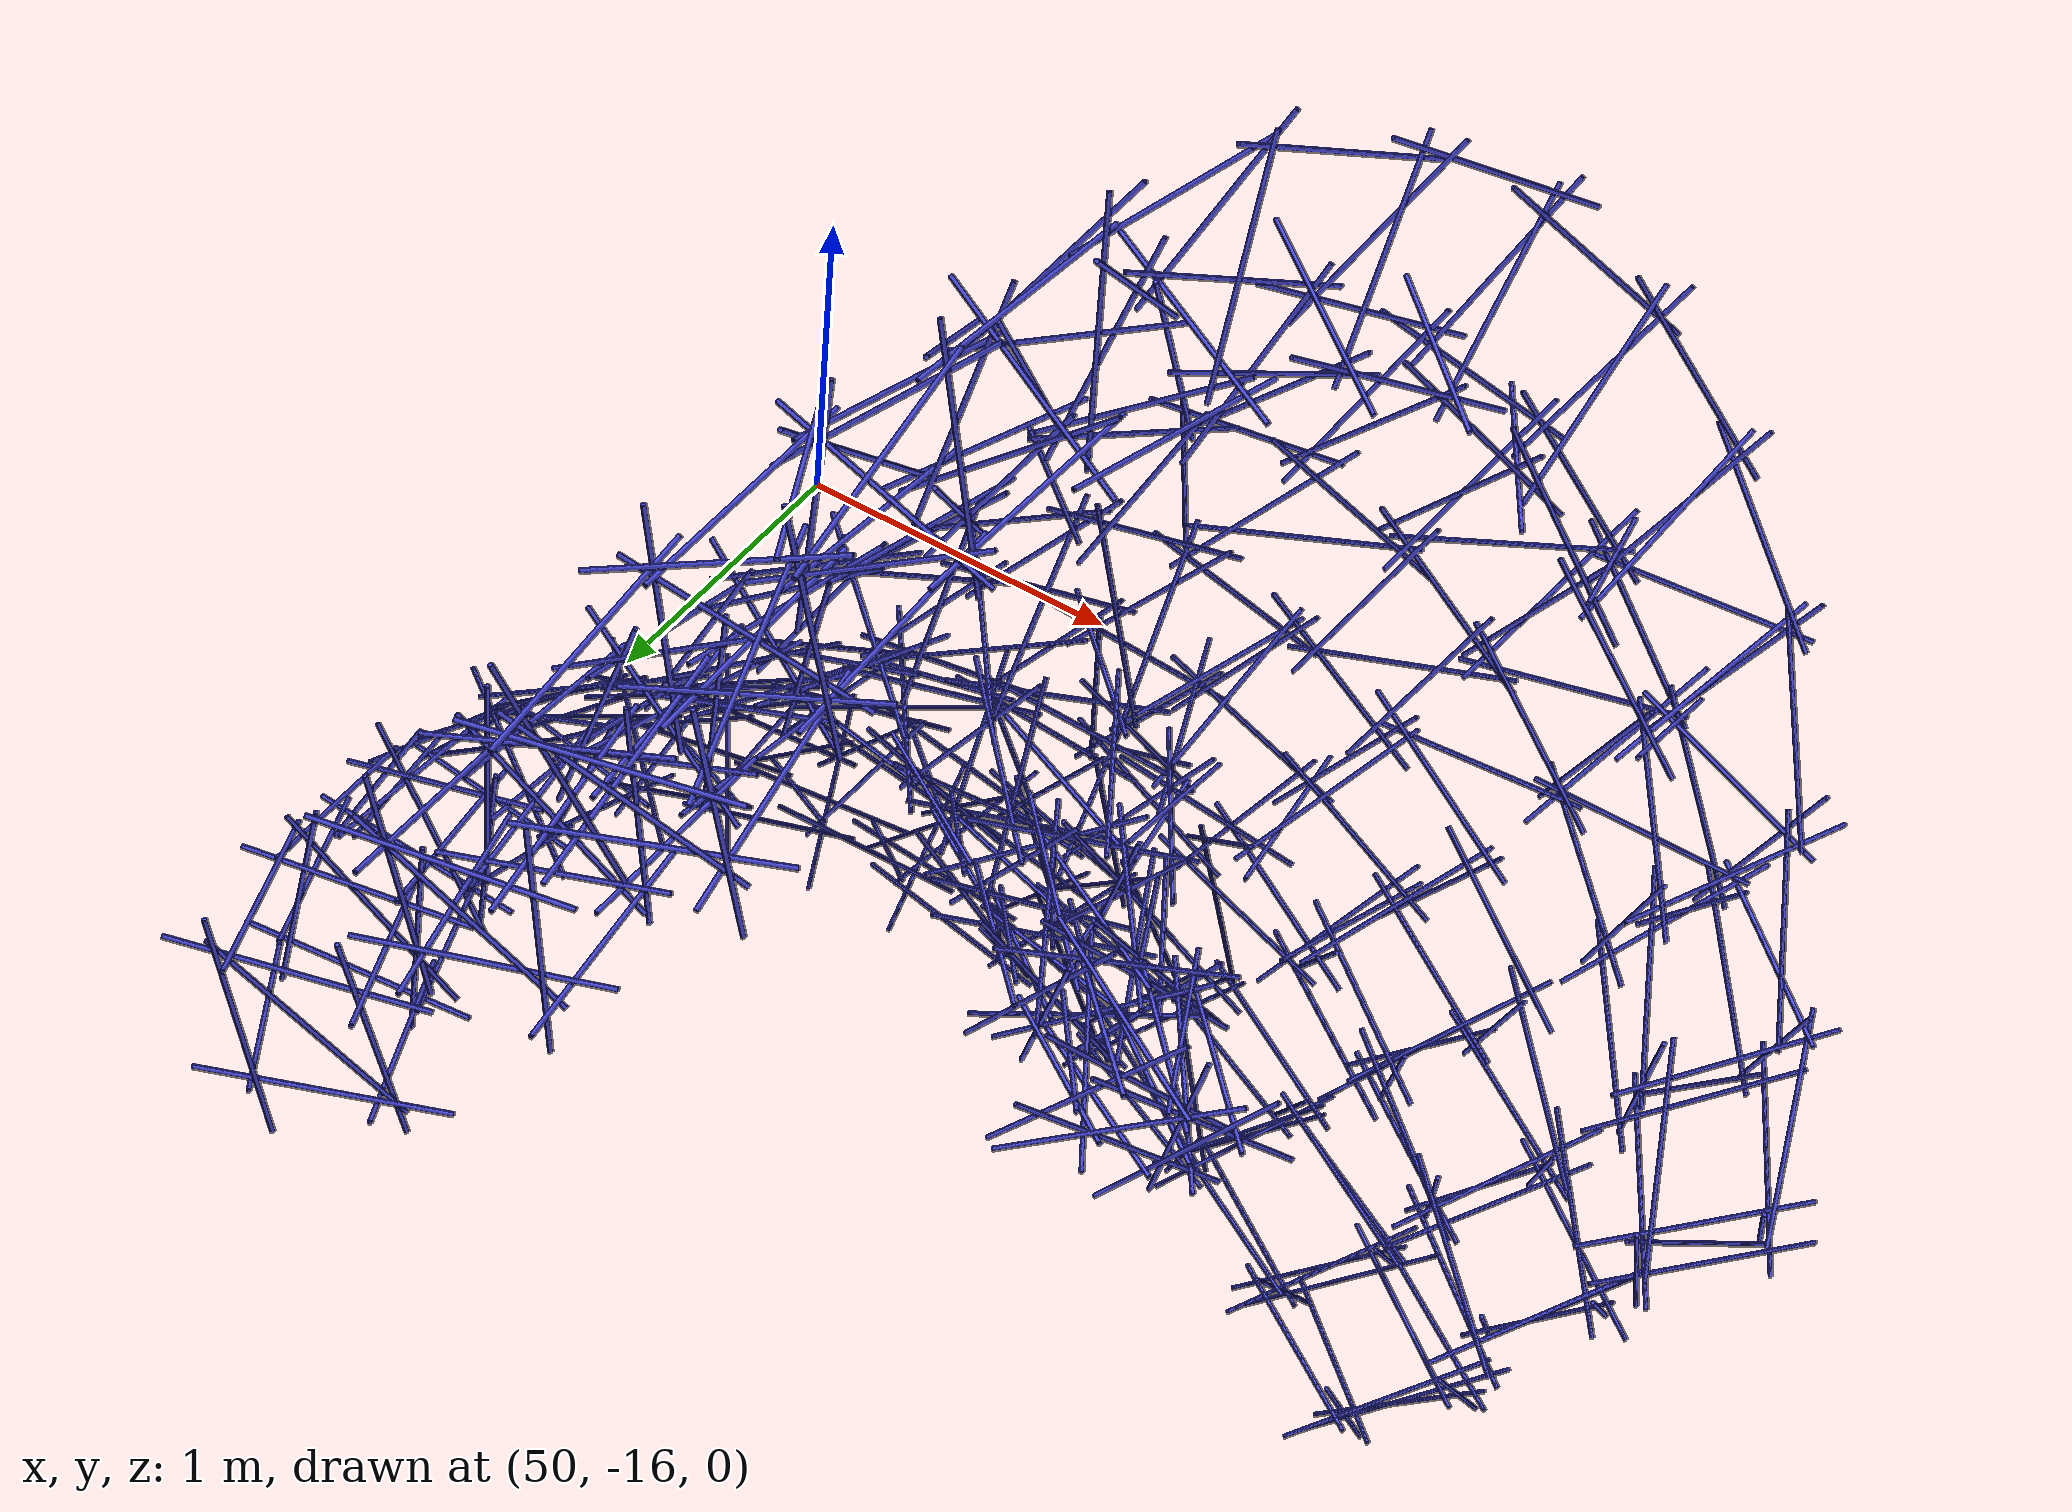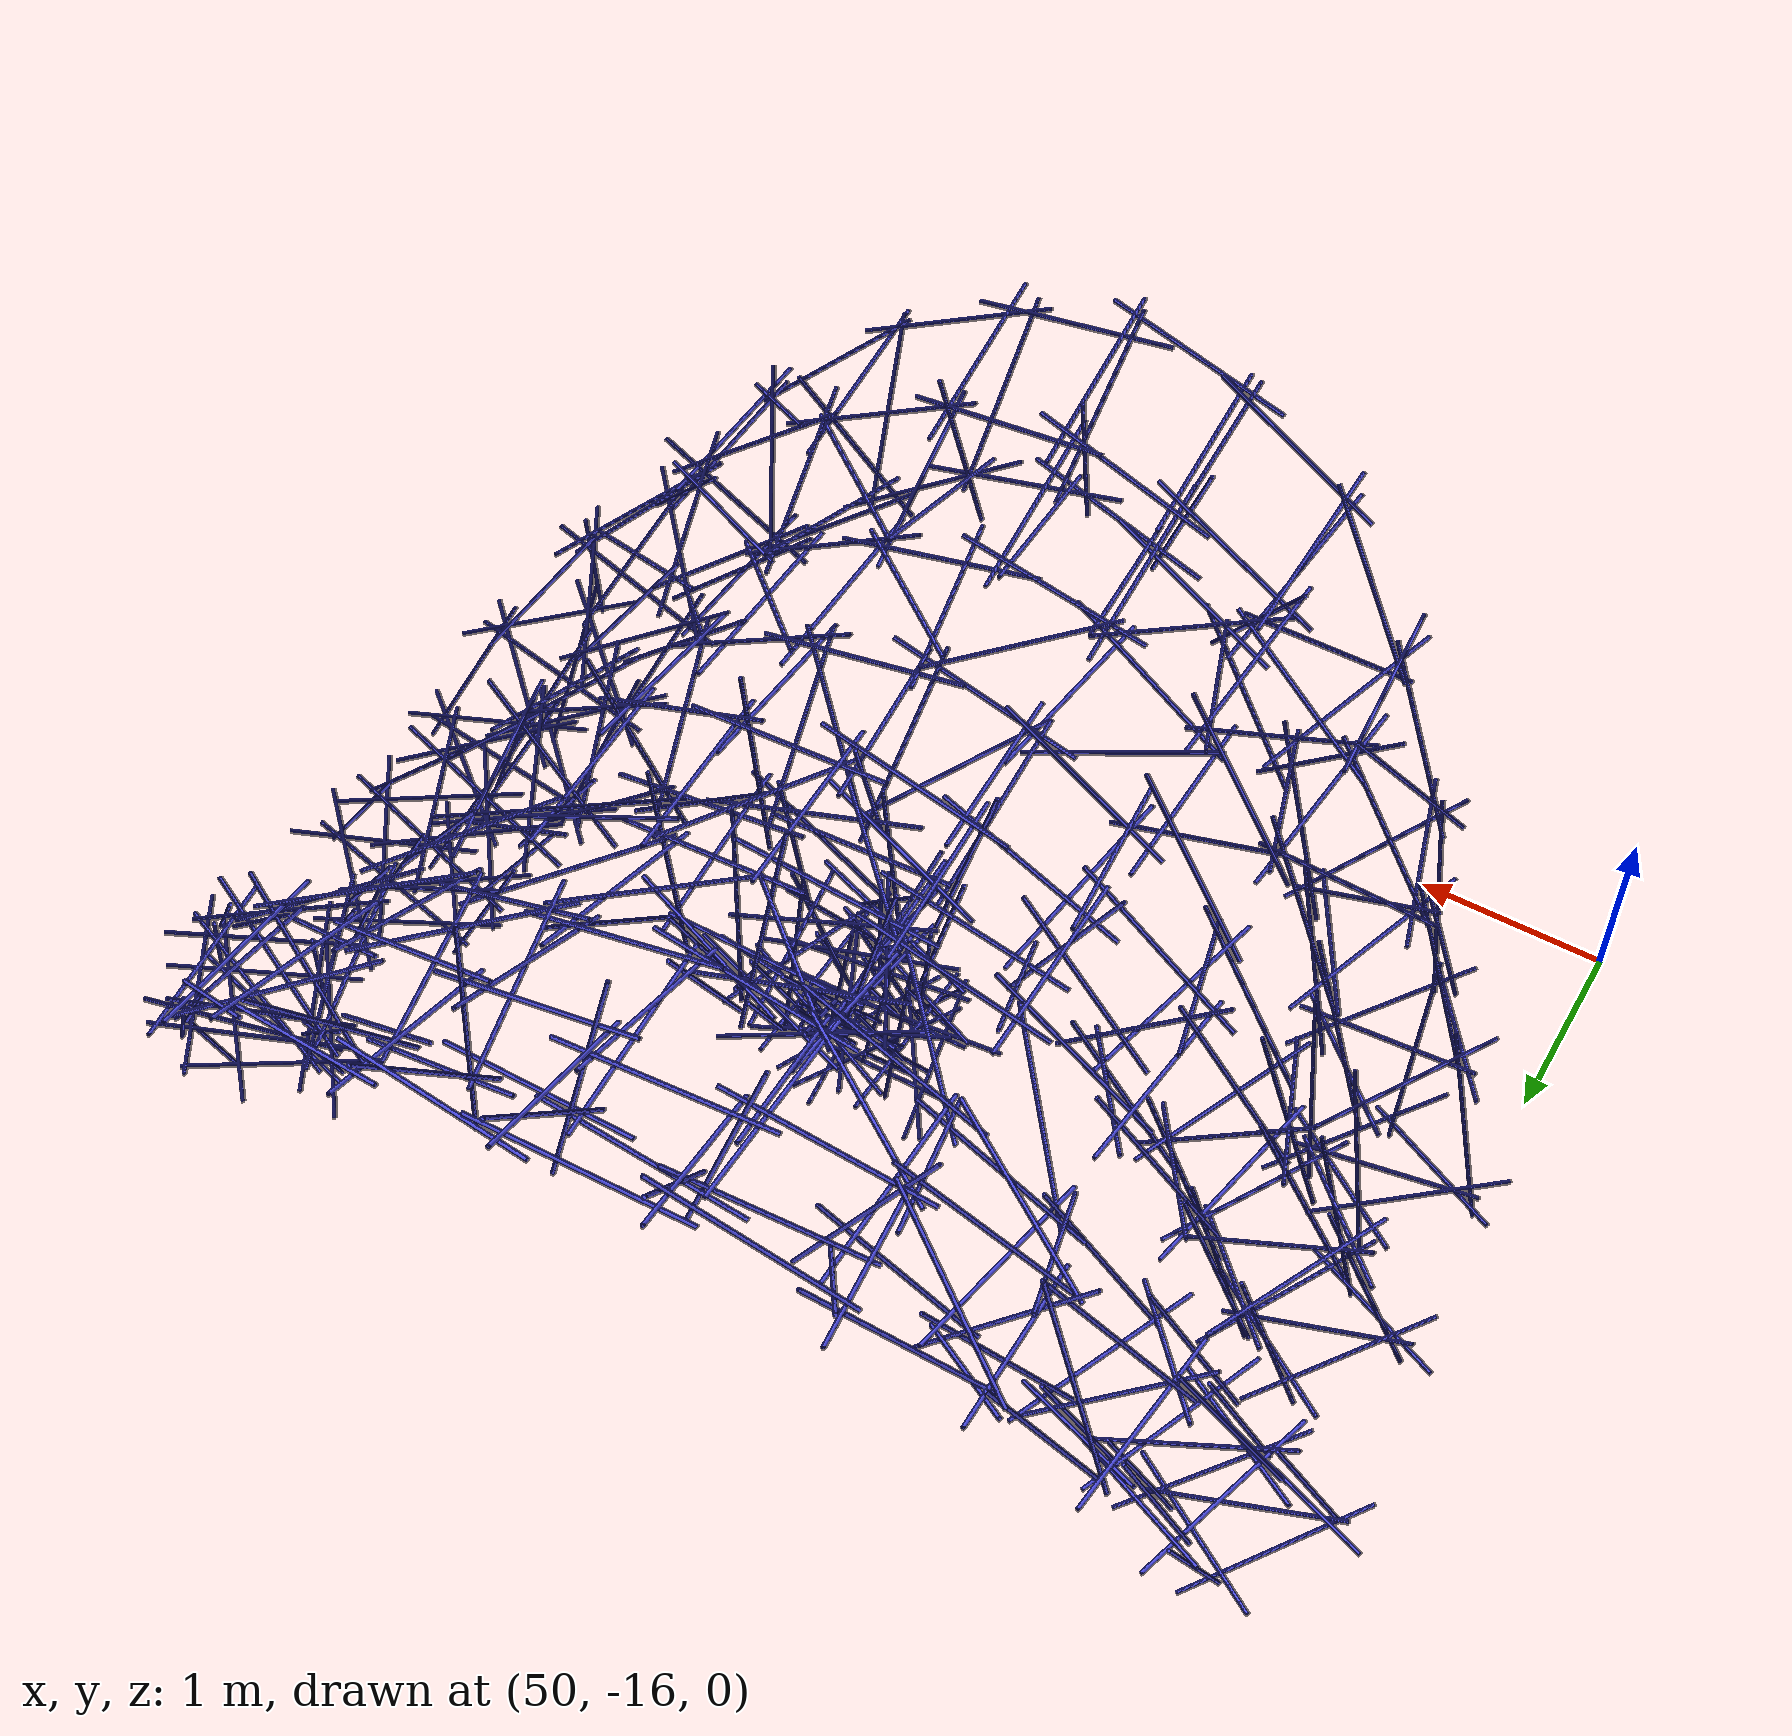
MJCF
<mujoco><worldbody><light diffuse=".5 .5 .5" pos="0 0 3" dir="0 0 -1" /><geom type="cylinder" size="0.01" rgba="0.3 .3 0.9 1" fromto="49.909153222877066 -13.285729749251018 0.3553573185139203 50.82626975844849 -13.211239473945874 -0.03623999897743446" /><geom type="cylinder" size="0.01" rgba="0.3 .3 0.9 1" fromto="56.13308463116423 -13.285729743952192 0.3553572906578495 55.2159680955928 -13.211239468647046 -0.03624002683350436" /><geom type="cylinder" size="0.01" rgba="0.3 .3 0.9 1" fromto="53.521118958236165 -13.58334839321621 -3.055401173623906e-06 52.521118958236165 -13.58334839321621 -3.055401173623906e-06" /><geom type="cylinder" size="0.01" rgba="0.3 .3 0.9 1" fromto="49.96106443141773 -14.218182559514881 0.2655678406144317 50.9169367584547 -14.242254515545184 -0.027226686892138918" /><geom type="cylinder" size="0.01" rgba="0.3 .3 0.9 1" fromto="56.081173487430966 -14.21818255952574 0.2655678404823487 55.12530116039399 -14.242254515556043 -0.027226687024221263" /><geom type="cylinder" size="0.01" rgba="0.3 .3 0.9 1" fromto="49.80578664842395 -12.358505864344968 0.27500358862179786 50.741778805674954 -12.179621349111915 -0.028177894609689336" /><geom type="cylinder" size="0.01" rgba="0.3 .3 0.9 1" fromto="56.23645123353301 -12.358505857211899 0.2750035765323522 55.300459076282 -12.179621341978846 -0.028177906699134114" /><geom type="cylinder" size="0.01" rgba="0.3 .3 0.9 1" fromto="53.627356698498815 -13.895243725695654 7.358189627160172e-06 52.62746876383741 -13.910214284437249 -1.476674209333062e-05" /><geom type="cylinder" size="0.01" rgba="0.3 .3 0.9 1" fromto="50.317796801035804 -13.59160616156146 -0.02980999585064925 50.67793050300794 -13.788481911722625 0.882080159651821" /><geom type="cylinder" size="0.01" rgba="0.3 .3 0.9 1" fromto="50.69638369747848 -13.224438759335957 -0.20541408756077928 51.125416677753286 -13.35152982469196 0.6888893077940575" /><geom type="cylinder" size="0.01" rgba="0.3 .3 0.9 1" fromto="50.87243349422475 -13.03223312456805 -0.11167372469277437 50.30808018993692 -13.79780141394312 0.1972122449509386" /><geom type="cylinder" size="0.01" rgba="0.3 .3 0.9 1" fromto="50.92455383955306 -13.395693737093683 -0.011399878104599859 50.16173899033237 -12.791585437931206 0.21917910769294813" /><geom type="cylinder" size="0.01" rgba="0.3 .3 0.9 1" fromto="51.07263388698333 -13.443690109854646 0.425082675581097 50.47570557955165 -12.710726836259138 0.7513363121078064" /><geom type="cylinder" size="0.01" rgba="0.3 .3 0.9 1" fromto="49.94621781619383 -13.296046190235435 0.12854548148715472 50.45925308306144 -13.37099804479039 0.9836343858993483" /><geom type="cylinder" size="0.01" rgba="0.3 .3 0.9 1" fromto="50.29692631507366 -13.265553728584194 0.6948733614314414 50.845772218279684 -13.322636145139837 1.5288456464950024" /><geom type="cylinder" size="0.01" rgba="0.3 .3 0.9 1" fromto="50.317504984450004 -12.932450251921223 -0.03470324001757863 50.6673312455276 -12.89317574564254 0.9012877322770453" /><geom type="cylinder" size="0.01" rgba="0.3 .3 0.9 1" fromto="50.56742951335638 -12.833403291775483 0.5598758567564655 50.97787718234827 -12.83049832415265 1.4717553839870272" /><geom type="cylinder" size="0.01" rgba="0.3 .3 0.9 1" fromto="50.20676498818122 -13.33466416150364 0.8966928594500564 51.10290270017376 -13.205991304553736 0.4719806074144868" /><geom type="cylinder" size="0.01" rgba="0.3 .3 0.9 1" fromto="49.77900948987501 -13.192914442259568 0.34810240476694676 50.57040521651835 -13.707872451934668 0.01869224687542803" /><geom type="cylinder" size="0.01" rgba="0.3 .3 0.9 1" fromto="50.1441154866743 -13.179190618866222 0.8734147933346088 50.79066015816407 -13.90304350638699 0.6325476411613946" /><geom type="cylinder" size="0.01" rgba="0.3 .3 0.9 1" fromto="49.86685523820776 -13.444281030016171 0.41169150318947856 50.522475408129765 -12.741542736027649 0.13542879677845754" /><geom type="cylinder" size="0.01" rgba="0.3 .3 0.9 1" fromto="50.228687299649394 -13.51207023180905 0.9245911087272409 50.71785651211376 -12.659898531014493 0.738803934945251" /><geom type="cylinder" size="0.01" rgba="0.3 .3 0.9 1" fromto="50.89116234410513 -13.231982486740096 0.376730317645001 51.41450970771235 -13.385822586870704 1.2148477083470326" /><geom type="cylinder" size="0.01" rgba="0.3 .3 0.9 1" fromto="51.179592704816216 -13.268485551093898 0.9113654158691772 51.78829449197155 -13.293662293973677 1.7043649530265892" /><geom type="cylinder" size="0.01" rgba="0.3 .3 0.9 1" fromto="51.34725662790377 -13.138827382414684 1.0755983502313207 50.881993400099724 -14.00643152133274 1.2510782265294813" /><geom type="cylinder" size="0.01" rgba="0.3 .3 0.9 1" fromto="51.37329352535214 -13.482998848824726 1.0636117286797666 50.893757360069905 -12.687569744922566 1.4342026174666125" /><geom type="cylinder" size="0.01" rgba="0.3 .3 0.9 1" fromto="50.69279174633851 -13.349037874072959 1.275395189661283 51.32155203513465 -13.384912053095244 2.0521664188610167" /><geom type="cylinder" size="0.01" rgba="0.3 .3 0.9 1" fromto="50.812487029391555 -12.888672895146263 1.2140713335658233 51.44159141600392 -12.825536990987926 1.9888238930008924" /><geom type="cylinder" size="0.01" rgba="0.3 .3 0.9 1" fromto="50.623185801610916 -13.418521678280126 1.5417849025252077 51.413294034457415 -13.297308274209833 0.9409219472168586" /><geom type="cylinder" size="0.01" rgba="0.3 .3 0.9 1" fromto="50.640780416151536 -13.159843017896073 1.416058708300943 50.96597772717512 -14.06662886327285 1.1477563797099504" /><geom type="cylinder" size="0.01" rgba="0.3 .3 0.9 1" fromto="50.74192370081881 -13.594235355684386 1.3833010581635463 50.98319404295985 -12.632274490656773 1.2551608374735799" /><geom type="cylinder" size="0.01" rgba="0.3 .3 0.9 1" fromto="50.61438155126154 -13.648657218050879 0.5321723816415993 51.05921554675067 -13.819374095436775 1.41136431986259" /><geom type="cylinder" size="0.01" rgba="0.3 .3 0.9 1" fromto="51.233450944616415 -13.210034347243685 1.96805699056554 51.45871084785185 -14.140775323694571 1.6799958672781088" /><geom type="cylinder" size="0.01" rgba="0.3 .3 0.9 1" fromto="51.63511842339539 -13.20575671735253 1.506157320967179 51.299508118825756 -14.107542438230338 1.7784590600133474" /><geom type="cylinder" size="0.01" rgba="0.3 .3 0.9 1" fromto="51.102483434186 -13.449587795568084 2.1064499821402993 51.85488354535653 -13.295748260196875 1.4659599587462298" /><geom type="cylinder" size="0.01" rgba="0.3 .3 0.9 1" fromto="51.2071153906509 -13.601303340699998 1.8926994538189594 51.33768711113231 -12.609967879364294 1.8783806232504376" /><geom type="cylinder" size="0.01" rgba="0.3 .3 0.9 1" fromto="51.7318093376633 -13.453030380337891 1.4897078675096485 51.24499769377987 -12.673462779706403 1.8837748407834605" /><geom type="cylinder" size="0.01" rgba="0.3 .3 0.9 1" fromto="50.86157344521668 -13.79652332682591 1.1473545830161365 51.50601520477469 -14.048660156223171 1.8692422735880578" /><geom type="cylinder" size="0.01" rgba="0.3 .3 0.9 1" fromto="51.16274366367822 -13.13340802285067 0.4935098948581076 50.577553079263936 -13.899726724768122 0.7586657490352617" /><geom type="cylinder" size="0.01" rgba="0.3 .3 0.9 1" fromto="55.272914511518024 -13.824683454360931 0.8295237821064358 55.67103977223834 -13.53714805381252 -0.04157877799073373" /><geom type="cylinder" size="0.01" rgba="0.3 .3 0.9 1" fromto="54.91483054459009 -13.32442816307551 0.6936056526937109 55.33355592101413 -13.23064751978795 -0.20965192412649802" /><geom type="cylinder" size="0.01" rgba="0.3 .3 0.9 1" fromto="54.937279355412656 -13.114032012695336 0.4296243418100989 55.46637462556936 -13.899091177960404 0.751711755614365" /><geom type="cylinder" size="0.01" rgba="0.3 .3 0.9 1" fromto="55.16089387916089 -13.043293824404442 -0.12374253613115194 55.719657181609385 -13.813482393897342 0.18381744055523463" /><geom type="cylinder" size="0.01" rgba="0.3 .3 0.9 1" fromto="55.13461821067488 -13.406622925005946 -0.045523379450670864 55.838697008591346 -12.787073532297198 0.3015091785589834" /><geom type="cylinder" size="0.01" rgba="0.3 .3 0.9 1" fromto="55.60777483837993 -13.315077829385135 1.0038235591217497 56.125144183665086 -13.341787484145605 0.14847827509793343" /><geom type="cylinder" size="0.01" rgba="0.3 .3 0.9 1" fromto="55.8262275494992 -13.129003390166272 0.9140381539435957 55.2135632742168 -13.835382311598018 0.5595366657244096" /><geom type="cylinder" size="0.01" rgba="0.3 .3 0.9 1" fromto="56.23135599440045 -13.153361101505686 0.3681967491704361 55.48985488560577 -13.718268540395972 0.0061806015434526795" /><geom type="cylinder" size="0.01" rgba="0.3 .3 0.9 1" fromto="56.154649721559466 -13.446973965335747 0.44042364414099455 55.50355394118402 -12.774731361276277 0.08805428386029535" /><geom type="cylinder" size="0.01" rgba="0.3 .3 0.9 1" fromto="54.963380385112195 -13.91989667981393 1.3830686583308784 55.37943547265775 -13.739152009713711 0.491873097099887" /><geom type="cylinder" size="0.01" rgba="0.3 .3 0.9 1" fromto="55.34956375105746 -12.827783125365562 0.8868985727651942 55.74159922233382 -12.898423394739252 -0.03033538953882542" /><geom type="cylinder" size="0.01" rgba="0.3 .3 0.9 1" fromto="54.36050120991304 -13.350681316844293 1.7746516410578785 54.8711170571448 -13.345874197541411 0.9148561141098752" /><geom type="cylinder" size="0.01" rgba="0.3 .3 0.9 1" fromto="54.63237325430005 -12.789493523079447 2.008781003081714 55.182138978499474 -12.818468922000168 1.1739648108855727" /><geom type="cylinder" size="0.01" rgba="0.3 .3 0.9 1" fromto="54.617250477338054 -13.326990471720537 1.2169500953002363 55.1536122458895 -13.23729630539958 0.37774153375885366" /><geom type="cylinder" size="0.01" rgba="0.3 .3 0.9 1" fromto="54.697993799639605 -13.14018069103593 1.0617504590750262 55.11389593692718 -14.013981793696468 1.3137366594687239" /><geom type="cylinder" size="0.01" rgba="0.3 .3 0.9 1" fromto="54.70491672760591 -13.495157607255889 1.029835868875551 55.28785298056843 -12.749187472367025 1.351882267451757" /><geom type="cylinder" size="0.01" rgba="0.3 .3 0.9 1" fromto="54.67886891884908 -13.418952730151492 2.016756423394232 55.31896802984392 -13.41591874442915 1.248470068553635" /><geom type="cylinder" size="0.01" rgba="0.3 .3 0.9 1" fromto="55.154919852413656 -13.368546900103524 1.4904389257918373 55.811001655330045 -13.36945127611956 0.7357496851198954" /><geom type="cylinder" size="0.01" rgba="0.3 .3 0.9 1" fromto="55.452687450564646 -13.353477769864439 1.506012937557543 54.57154583022593 -13.266952122819774 1.041144399893018" /><geom type="cylinder" size="0.01" rgba="0.3 .3 0.9 1" fromto="55.41983321124141 -13.182474774970315 1.4467870618329874 54.93453826196749 -14.003822437925663 1.1469924175062338" /><geom type="cylinder" size="0.01" rgba="0.3 .3 0.9 1" fromto="55.3191657968864 -13.572928493915564 1.494959937868978 54.982329609082 -12.655755062403143 1.2820414578980435" /><geom type="cylinder" size="0.01" rgba="0.3 .3 0.9 1" fromto="54.52313532861131 -14.03602785822606 1.8691357850334869 55.17859528830106 -13.925353580345552 1.122059185574542" /><geom type="cylinder" size="0.01" rgba="0.3 .3 0.9 1" fromto="55.04202727360667 -12.860951819418712 1.465354288876056 55.47949007115841 -12.977257977382548 0.5736709491315594" /><geom type="cylinder" size="0.01" rgba="0.3 .3 0.9 1" fromto="54.36625285066699 -13.460530904822818 1.4484218663425763 54.83660712474845 -12.712506883453445 1.9166386113525078" /><geom type="cylinder" size="0.01" rgba="0.3 .3 0.9 1" fromto="54.971029386103844 -13.424422524057942 2.076181795266459 54.213649369691055 -13.265092000383268 1.4429446398782788" /><geom type="cylinder" size="0.01" rgba="0.3 .3 0.9 1" fromto="54.8623658752446 -13.263155579957836 1.941405354987717 54.65825011436075 -14.20364523097994 1.6697144046799686" /><geom type="cylinder" size="0.01" rgba="0.3 .3 0.9 1" fromto="54.38752285571787 -13.207044888670826 1.5267696759870906 54.70440811854746 -14.117617355847882 1.7921778752208497" /><geom type="cylinder" size="0.01" rgba="0.3 .3 0.9 1" fromto="54.783938952052836 -13.595507874303932 2.006275904373551 54.6660321038297 -12.618878779350137 1.8265717418401906" /><geom type="cylinder" size="0.01" rgba="0.3 .3 0.9 1" fromto="55.79907375202693 -13.540175640707004 0.8433570475416571 55.31629287394866 -12.694439520222925 0.6160839997103814" /><geom type="cylinder" size="0.01" rgba="0.3 .3 0.9 1" fromto="54.908985300036385 -13.436836734382911 0.5278478624407652 55.54945741976561 -12.728687066650636 0.8250338512427506" /><geom type="cylinder" size="0.01" rgba="0.3 .3 0.9 1" fromto="55.81067627116846 -13.295967992421513 0.9513101624541014 54.936370813743565 -13.206187078598935 0.47430979072444557" /><geom type="cylinder" size="0.01" rgba="0.3 .3 0.9 1" fromto="51.667806317323986 -12.803479697265036 2.2847439562499585 52.584546697555616 -12.742221687864378 2.6795027833039398" /><geom type="cylinder" size="0.01" rgba="0.3 .3 0.9 1" fromto="52.08369128121324 -13.490818393890837 1.86935552856065 51.85937591908629 -12.677627573446234 2.4063874716129146" /><geom type="cylinder" size="0.01" rgba="0.3 .3 0.9 1" fromto="51.81152953987981 -13.613058972966787 2.3412812477733222 51.850622643096976 -12.61412162939206 2.3168699206336765" /><geom type="cylinder" size="0.01" rgba="0.3 .3 0.9 1" fromto="51.65774438268199 -13.443643819239428 2.539741383481166 52.13361468445408 -13.331682616384002 1.6673812829799428" /><geom type="cylinder" size="0.01" rgba="0.3 .3 0.9 1" fromto="51.82983677238205 -13.304889885980204 2.3904199040122585 51.92578760302467 -14.28316074179852 2.2066277095221416" /><geom type="cylinder" size="0.01" rgba="0.3 .3 0.9 1" fromto="52.140200917923636 -13.296523492174094 1.871064653264724 51.870782837512564 -14.191173638311662 2.227456311365253" /><geom type="cylinder" size="0.01" rgba="0.3 .3 0.9 1" fromto="51.72587696240883 -14.015291849908522 2.101113604483837 52.59101166480177 -14.106001074871763 2.5943820742060058" /><geom type="cylinder" size="0.01" rgba="0.3 .3 0.9 1" fromto="51.66351554728124 -13.433147342434449 2.2449615564045384 52.60140896811515 -13.541673364107035 2.574473367689631" /><geom type="cylinder" size="0.01" rgba="0.3 .3 0.9 1" fromto="52.42013022265729 -13.61752748402615 2.550241971386241 52.370360210013075 -12.622961259677417 2.64168031797072" /><geom type="cylinder" size="0.01" rgba="0.3 .3 0.9 1" fromto="52.23037948199982 -12.83038265201209 2.566204189610097 53.221454896419196 -12.816906488656569 2.6988236299447586" /><geom type="cylinder" size="0.01" rgba="0.3 .3 0.9 1" fromto="52.428643037291835 -12.810882104160036 2.8368051326445505 52.61411774279128 -12.69565559732108 1.8609352715761884" /><geom type="cylinder" size="0.01" rgba="0.3 .3 0.9 1" fromto="52.36985846737261 -12.74086486874121 2.5518860492593713 53.012878517695384 -13.426481716994465 2.5444865712935965" /><geom type="cylinder" size="0.01" rgba="0.3 .3 0.9 1" fromto="53.270869928790205 -12.448073559014151 2.1228732811279905 52.324438394275944 -12.770767963292291 2.1345211103060526" /><geom type="cylinder" size="0.01" rgba="0.3 .3 0.9 1" fromto="53.71288928015635 -12.787621294479095 2.1254657013315446 52.79740720662602 -12.38862976294062 2.177411161240866" /><geom type="cylinder" size="0.01" rgba="0.3 .3 0.9 1" fromto="53.000366709530134 -13.528797440308487 2.6097072768740865 53.59133744856475 -12.72280876537199 2.5760050294863466" /><geom type="cylinder" size="0.01" rgba="0.3 .3 0.9 1" fromto="52.99628308918151 -12.86799638502448 2.8368277896370273 52.982675619682716 -12.401678600494519 1.9523151777399956" /><geom type="cylinder" size="0.01" rgba="0.3 .3 0.9 1" fromto="52.820756884804105 -12.716933682953991 2.689583321781384 53.79787305378558 -12.794993510530508 2.4917180756321433" /><geom type="cylinder" size="0.01" rgba="0.3 .3 0.9 1" fromto="53.69467085649079 -12.874027094132996 2.805059535263189 53.42837135738356 -12.680347608578646 1.8608281898553791" /><geom type="cylinder" size="0.01" rgba="0.3 .3 0.9 1" fromto="53.482056842380224 -12.771164673729231 2.726611168933263 54.3466401869498 -12.729523923112174 2.2258500600390767" /><geom type="cylinder" size="0.01" rgba="0.3 .3 0.9 1" fromto="53.903471018593386 -13.437852640257843 1.825368977510799 54.20114755677277 -12.68841551860528 2.416750985443624" /><geom type="cylinder" size="0.01" rgba="0.3 .3 0.9 1" fromto="54.15768474560268 -13.613616138412052 2.301625535253828 54.19158755073504 -12.614602451995381 2.2729505608626703" /><geom type="cylinder" size="0.01" rgba="0.3 .3 0.9 1" fromto="54.22930022655916 -13.25836084693055 2.3025267175568764 54.16293024960704 -14.247594780317023 2.172099530221948" /><geom type="cylinder" size="0.01" rgba="0.3 .3 0.9 1" fromto="54.40556526379716 -13.460970525485791 2.5235854463012743 53.893215940162804 -13.407613011454279 1.6664675161027536" /><geom type="cylinder" size="0.01" rgba="0.3 .3 0.9 1" fromto="53.46712993761443 -13.456311329131916 2.6604548496923925 54.37361393578443 -13.485993340259776 2.2392592427861144" /><geom type="cylinder" size="0.01" rgba="0.3 .3 0.9 1" fromto="53.61642526719585 -13.615786308317892 2.53814262898991 53.58130043750703 -12.621513473486862 2.6390771436833402" /><geom type="cylinder" size="0.01" rgba="0.3 .3 0.9 1" fromto="53.61032011921586 -13.291019924814234 2.526380603745434 53.57063727061849 -14.282454802493177 2.401953296256537" /><geom type="cylinder" size="0.01" rgba="0.3 .3 0.9 1" fromto="53.42746666866425 -14.170194463564943 2.535172344392186 54.310890065607026 -14.026363496195103 2.089217464881332" /><geom type="cylinder" size="0.01" rgba="0.3 .3 0.9 1" fromto="52.811832441304745 -14.124419017800673 2.5835102262205147 53.80098838968103 -14.028704907604553 2.472113103721012" /><geom type="cylinder" size="0.01" rgba="0.3 .3 0.9 1" fromto="52.821363322551505 -13.420156324666612 2.660286343827586 53.81865161005484 -13.425432045207621 2.586881722846175" /><geom type="cylinder" size="0.01" rgba="0.3 .3 0.9 1" fromto="52.22154702713922 -13.433756133923515 2.5703821931707314 53.20388143604782 -13.522429302300026 2.7351735105520207" /><geom type="cylinder" size="0.01" rgba="0.3 .3 0.9 1" fromto="52.24364355080448 -14.134027806100713 2.400973461759601 53.221598797965925 -14.207342870671125 2.596494396332948" /><geom type="cylinder" size="0.01" rgba="0.3 .3 0.9 1" fromto="52.454128837291734 -13.298227781105174 2.5930561952196607 52.499305331295126 -14.289731779476021 2.471077075677904" /><geom type="cylinder" size="0.01" rgba="0.3 .3 0.9 1" fromto="51.82916713894178 -13.322524340552105 1.8883138157611732 52.80885042863338 -13.355021866492379 2.086214201578919" /><geom type="cylinder" size="0.01" rgba="0.3 .3 0.9 1" fromto="52.572593470480044 -13.473667037549733 1.9811191158771988 52.42723615568901 -12.695858679082733 2.5925808142161957" /><geom type="cylinder" size="0.01" rgba="0.3 .3 0.9 1" fromto="52.32275106118303 -13.514517930308026 2.765497321238305 52.5405373908883 -13.38956605575254 1.7975323716463407" /><geom type="cylinder" size="0.01" rgba="0.3 .3 0.9 1" fromto="52.615565763425835 -13.605994793945332 1.9978690405341475 52.616587217901674 -12.60718660309214 2.0466661153986285" /><geom type="cylinder" size="0.01" rgba="0.3 .3 0.9 1" fromto="52.54458929755419 -13.386358299315733 1.9452850721299686 52.40161013834427 -14.19119977575032 2.521294757675461" /><geom type="cylinder" size="0.01" rgba="0.3 .3 0.9 1" fromto="52.427261363023604 -14.222769378226191 2.4621274990705566 53.08613037484264 -13.654588186024442 1.9691145599981552" /><geom type="cylinder" size="0.01" rgba="0.3 .3 0.9 1" fromto="53.037774491845624 -13.566150939414129 1.9131951008296688 52.958557038932256 -14.235701361792023 2.6517252810169794" /><geom type="cylinder" size="0.01" rgba="0.3 .3 0.9 1" fromto="53.633792873534475 -14.13135158523513 2.5267022798588443 53.01578609751289 -13.571605309910082 1.974659045998362" /><geom type="cylinder" size="0.01" rgba="0.3 .3 0.9 1" fromto="53.41710306772516 -13.367198193821524 1.9717539729467473 53.54364092892112 -14.221063889986238 2.476631723097314" /><geom type="cylinder" size="0.01" rgba="0.3 .3 0.9 1" fromto="53.22850845899708 -13.376670403852751 2.046201351814293 54.21786795034518 -13.364017382018568 1.9012610264459453" /><geom type="cylinder" size="0.01" rgba="0.3 .3 0.9 1" fromto="52.50860066938392 -13.466381629193824 2.0480472696034058 53.44647021266425 -13.46229065137226 1.9849284634708444" /><geom type="cylinder" size="0.01" rgba="0.3 .3 0.9 1" fromto="52.32754989018174 -13.330258893407906 2.0605718248270293 53.26469295261098 -13.673966978132608 2.1208016599226163" /><geom type="cylinder" size="0.01" rgba="0.3 .3 0.9 1" fromto="52.77446096129112 -13.68199106370668 2.05585682707727 53.699202180760416 -13.304614784913808 2.105261495064087" /><geom type="cylinder" size="0.01" rgba="0.3 .3 0.9 1" fromto="52.52140102973657 -12.685891982108057 2.087222547951843 53.52138124049613 -12.69093565271178 2.0909827974265123" /><geom type="cylinder" size="0.01" rgba="0.3 .3 0.9 1" fromto="53.5146882500333 -12.621219718543832 2.0472617672809212 53.54807243715812 -13.620568862985245 2.0335948892822193" /><geom type="cylinder" size="0.01" rgba="0.3 .3 0.9 1" fromto="53.050113942993825 -13.620302253960686 2.6621403044269245 53.02616317212606 -12.624609192396798 2.751704179557324" /><geom type="cylinder" size="0.01" rgba="0.3 .3 0.9 1" fromto="52.9950747303898 -13.304651068916211 2.5912741616149475 53.081964634286365 -14.296741531699654 2.5006835536305645" /><geom type="cylinder" size="0.01" rgba="0.3 .3 0.9 1" fromto="52.96710375564678 -13.4079810843419 2.816563861124756 52.99593773771449 -13.697196923993566 1.859734304948369" /><geom type="cylinder" size="0.01" rgba="0.3 .3 0.9 1" fromto="53.62423046686196 -13.535151047803176 2.783309411551814 53.42239854838031 -13.39275222512544 1.8142962785231584" /><geom type="cylinder" size="0.01" rgba="0.3 .3 0.9 1" fromto="53.958145016521854 -13.277500553749103 1.868460496773101 54.22062332560943 -14.196911284174043 2.1613581683889858" /><geom type="cylinder" size="0.01" rgba="0.3 .3 0.9 1" fromto="53.499445467653636 -13.515874866452403 2.039603616582262 53.693691498830326 -12.757912050647679 2.6623080803766666" /><geom type="cylinder" size="0.01" rgba="0.3 .3 0.9 1" fromto="53.23157012935696 -13.973854502535385 0.6996287446004473 53.2648830892033 -12.976495507952983 0.7641677454592679" /><geom type="cylinder" size="0.01" rgba="0.3 .3 0.9 1" fromto="52.6630958546565 -13.881582267153787 0.7228746406514892 53.598663004395256 -13.532435033464886 0.7758870687894459" /><geom type="cylinder" size="0.01" rgba="0.3 .3 0.9 1" fromto="52.43131182052762 -13.551320423250184 0.6701775674308014 53.349507999425015 -13.94669775801718 0.6945197162836281" /><geom type="cylinder" size="0.01" rgba="0.3 .3 0.9 1" fromto="52.73363022082227 -12.965196520110814 0.6764703779589372 52.70854047867781 -13.957167857601018 0.5525213140777616" /><geom type="cylinder" size="0.01" rgba="0.3 .3 0.9 1" fromto="53.392276319424944 -13.09662027573694 0.7152230761364762 52.461074451099236 -13.428000196702245 0.8670467515225453" /><geom type="cylinder" size="0.01" rgba="0.3 .3 0.9 1" fromto="53.57210594216833 -13.46244423984123 0.8295688065514697 52.65668413986337 -13.088303695014687 0.6811714461246435" /><geom type="cylinder" size="0.01" rgba="0.3 .3 0.9 1" fromto="53.252352241028014 -13.910925852039778 0.6435648597715254 52.84430202159524 -12.998827425652575 0.6832067442228573" /><geom type="cylinder" size="0.01" rgba="0.3 .3 0.9 1" fromto="52.52797408293433 -13.73575855518828 0.7405040759417423 53.52214374528461 -13.665050769874586 0.6590971256342797" /><geom type="cylinder" size="0.01" rgba="0.3 .3 0.9 1" fromto="53.05120348854626 -12.921121090482142 0.6864265186710058 52.608579097375795 -13.802588455312168 0.5218089829082972" /><geom type="cylinder" size="0.01" rgba="0.3 .3 0.9 1" fromto="53.369984709351804 -13.445032775255696 1.45729964286695 52.923931605425885 -13.848298416523205 0.6582918512584109" /><geom type="cylinder" size="0.01" rgba="0.3 .3 0.9 1" fromto="52.76144406323737 -13.539408691988925 1.523760673741243 52.8617766140137 -13.264671625604503 0.5674903544229047" /><geom type="cylinder" size="0.01" rgba="0.3 .3 0.9 1" fromto="52.92584415405276 -12.803044610673716 1.450964823996691 53.196938331627635 -13.424353288815691 0.7157890128124036" /><geom type="cylinder" size="0.01" rgba="0.3 .3 0.9 1" fromto="53.305792499986026 -13.494457534783002 1.5324217707965815 53.28699919591441 -13.242373893346556 0.5648988256204928" /><geom type="cylinder" size="0.01" rgba="0.3 .3 0.9 1" fromto="52.77519589658682 -13.388148706447637 1.4653637421684256 53.01383609186965 -13.795844761283965 0.5839814278086068" /><geom type="cylinder" size="0.01" rgba="0.3 .3 0.9 1" fromto="52.97303633755461 -12.867013107694994 1.5333766362647983 52.69238892555894 -13.357571957915583 0.7083984276978166" /><geom type="cylinder" size="0.01" rgba="0.3 .3 0.9 1" fromto="53.31277620277209 -13.666127647286999 -0.15711073445545165 53.18855177263748 -13.744449091634513 0.8320475149228015" /><geom type="cylinder" size="0.01" rgba="0.3 .3 0.9 1" fromto="52.984600972908446 -14.038896857355464 -0.1133041293505912 52.58286210677205 -13.769561007443736 0.7619467394794628" /><geom type="cylinder" size="0.01" rgba="0.3 .3 0.9 1" fromto="52.72600335229904 -13.694252169313843 -0.009714961635283847 53.00933498975025 -13.25027837462117 0.8403500081437345" /><geom type="cylinder" size="0.01" rgba="0.3 .3 0.9 1" fromto="52.92674155598208 -13.985088589293671 -0.08413816776673388 53.246212332992414 -13.822265759264758 0.8493644560419997" /><geom type="cylinder" size="0.01" rgba="0.3 .3 0.9 1" fromto="52.88232824650895 -13.524841880720873 -0.14281215563447458 52.81956761141383 -13.677322822760988 0.8434994913600324" /><geom type="cylinder" size="0.01" rgba="0.3 .3 0.9 1" fromto="53.15810458401879 -13.596295101654045 -0.1044778199966796 52.95107045891545 -13.15120735380396 0.7667476202634383" /><geom type="cylinder" size="0.01" rgba="0.3 .3 0.9 1" fromto="52.805035892379536 -13.602367962878274 0.8140450504282065 52.69876177047374 -14.006892636968997 -0.09428616618000141" /><geom type="cylinder" size="0.01" rgba="0.3 .3 0.9 1" fromto="52.63083648754725 -13.513838652386953 1.5197451300140492 52.75897859847347 -13.666846568439382 0.5398634141765375" /><geom type="cylinder" size="0.01" rgba="0.3 .3 0.9 1" fromto="52.81627932150872 -13.208098685299817 0.762505545556496 52.83407479662726 -13.695909933837973 -0.11026218234420448" /><geom type="cylinder" size="0.01" rgba="0.3 .3 0.9 1" fromto="52.75976193362395 -12.97173611527611 1.5254668625832029 52.68596339046369 -13.353783829773683 0.6042756126928199" /><geom type="cylinder" size="0.01" rgba="0.3 .3 0.9 1" fromto="52.981440898002546 -13.66225538211487 1.5265375833605763 53.02503041364126 -13.724930953234189 0.5294559784198121" /><geom type="cylinder" size="0.01" rgba="0.3 .3 0.9 1" fromto="52.954814972925604 -12.827793218084826 1.5374374268656053 52.92047352708511 -13.292088925951404 0.6524232118643676" /><geom type="cylinder" size="0.01" rgba="0.3 .3 0.9 1" fromto="53.346594251805506 -13.66569976714555 0.8274263024444145 53.29417931830393 -13.977898688241451 -0.12114341476807455" /><geom type="cylinder" size="0.01" rgba="0.3 .3 0.9 1" fromto="53.19994093356515 -13.320980986294103 0.8486049150463286 53.260117229324955 -13.715721533195486 -0.06821497678664579" /><geom type="cylinder" size="0.01" rgba="0.3 .3 0.9 1" fromto="53.37025037669507 -13.497272565393072 1.5224887035110755 53.17221312911455 -13.654172491040578 0.5549331950762675" /><geom type="cylinder" size="0.01" rgba="0.3 .3 0.9 1" fromto="53.27689929873919 -12.960260419547707 1.5390110791567515 53.17809077730045 -13.3262839490389 0.6136659262814045" /><geom type="cylinder" size="0.01" rgba="0.3 .3 0.9 1" fromto="52.58691750828893 -13.356952942093846 -0.06884598713286305 53.122318350634245 -14.201446303273427 -0.08214639838729676" /><geom type="cylinder" size="0.01" rgba="0.3 .3 0.9 1" fromto="52.93972024228156 -14.207947701316678 0.03599519418709929 53.39142661739087 -13.31578104050121 0.03599906560647059" /><geom type="cylinder" size="0.01" rgba="0.3 .3 0.9 1" fromto="52.8059657443604 -14.24982681913026 0.04269919347740547 52.62936067813409 -13.265594748274001 0.03280569656268817" /><geom type="cylinder" size="0.01" rgba="0.3 .3 0.9 1" fromto="53.1701881426688 -13.245856988066906 -0.03600499730672446 53.24720153921234 -14.242887046161611 -0.03600208251601478" /><geom type="cylinder" size="0.01" rgba="0.3 .3 0.9 1" fromto="53.083079812139026 -13.665367686577804 0.8085465356457271 53.01495189664811 -13.98865265347668 -0.13529954148128787" /><geom type="cylinder" size="0.01" rgba="0.3 .3 0.9 1" fromto="53.41620132339488 -13.842635130309587 0.05456096229026075 52.4195834578573 -13.90072726963873 0.11268267457992831" /><geom type="cylinder" size="0.01" rgba="0.3 .3 0.9 1" fromto="52.39206251083598 -13.410199444781602 1.3389689939469056 53.334275302276865 -13.745176116559634 1.3440370319982629" /><geom type="cylinder" size="0.01" rgba="0.3 .3 0.9 1" fromto="52.54117822136582 -12.919067075648993 1.3918838013806174 53.0156316097175 -13.799280267741317 1.402779614716498" /><geom type="cylinder" size="0.01" rgba="0.3 .3 0.9 1" fromto="52.81032651527297 -12.737669082190063 1.4561316618103708 52.72687090611977 -13.716546073859028 1.2694903039017165" /><geom type="cylinder" size="0.01" rgba="0.3 .3 0.9 1" fromto="53.28891637655006 -12.65295334276064 1.306355408930096 52.392440608774066 -13.06829693483115 1.4606956121060757" /><geom type="cylinder" size="0.01" rgba="0.3 .3 0.9 1" fromto="53.51668080666858 -13.077815673332813 1.4271833295395948 52.52568391860197 -12.981796811101539 1.3338798143962423" /><geom type="cylinder" size="0.01" rgba="0.3 .3 0.9 1" fromto="53.63110546275242 -13.10523616587007 1.3188555790949832 52.69563592268307 -12.752508363332275 1.3407607592879804" /><geom type="cylinder" size="0.01" rgba="0.3 .3 0.9 1" fromto="52.99011660476183 -13.777095298343609 1.2758346488168661 53.37606704959577 -12.854628891262264 1.2659360661444448" /><geom type="cylinder" size="0.01" rgba="0.3 .3 0.9 1" fromto="52.678558158515195 -13.675749740244122 1.3029163495406637 53.590789501623966 -13.266251037207118 1.3149491738549366" /><geom type="cylinder" size="0.01" rgba="0.3 .3 0.9 1" fromto="53.277979264326824 -13.736502355585925 1.3341450900536613 53.16395822853659 -12.743778457613782 1.372855111912578" /><geom type="cylinder" size="0.01" rgba="0.3 .3 0.9 1" fromto="51.41736012945303 -13.343643888357988 1.487142020261852 52.18708281816437 -13.542712348035412 2.0936885814132986" /><geom type="cylinder" size="0.01" rgba="0.3 .3 0.9 1" fromto="51.09047794414917 -13.493913097843805 1.8628841622250005 51.95601136492936 -13.662966289739218 2.334342448632734" /><geom type="cylinder" size="0.01" rgba="0.3 .3 0.9 1" fromto="53.30571371180289 -12.905506789697371 1.2597174145283356 53.6088601388306 -13.382667581736648 2.084593055046822" /><geom type="cylinder" size="0.01" rgba="0.3 .3 0.9 1" fromto="53.08416163863554 -13.625383712594862 1.3039966789697932 52.60492220228736 -13.285458144262357 2.113181559354062" /><geom type="cylinder" size="0.01" rgba="0.3 .3 0.9 1" fromto="52.644740051123655 -13.05817636670275 1.364461274046556 52.88468751788816 -12.608886106801174 2.1545014474243858" /><geom type="cylinder" size="0.01" rgba="0.3 .3 0.9 1" fromto="52.97586179624046 -13.714843508821648 1.300268406385953 53.61442591139593 -13.580979443200711 2.0581049869039103" /><geom type="cylinder" size="0.01" rgba="0.3 .3 0.9 1" fromto="52.843672587935345 -12.935945738191172 1.3418353397371192 52.639007834256184 -13.613927072048142 2.047847839302795" /><geom type="cylinder" size="0.01" rgba="0.3 .3 0.9 1" fromto="53.2853192565759 -12.978598620788963 1.4124146872267294 53.0323842106368 -12.454711981812055 2.150768702613157" /><geom type="cylinder" size="0.01" rgba="0.3 .3 0.9 1" fromto="52.41869010346141 -13.416371892573071 2.172440228465007 52.64206626953438 -13.454899233417715 1.1984696270411341" /><geom type="cylinder" size="0.01" rgba="0.3 .3 0.9 1" fromto="52.50042167682635 -12.69619758594015 2.236681761221205 52.615481544917486 -13.144988441065337 1.3504831406451778" /><geom type="cylinder" size="0.01" rgba="0.3 .3 0.9 1" fromto="52.979071962268236 -13.674362582296796 2.212334343588866 52.895574673052025 -13.683066146445572 1.2158643487246694" /><geom type="cylinder" size="0.01" rgba="0.3 .3 0.9 1" fromto="53.41435823563621 -13.483418074040072 2.218063097605894 53.33156014580731 -13.574245111864535 1.2256443727116486" /><geom type="cylinder" size="0.01" rgba="0.3 .3 0.9 1" fromto="53.46479524476747 -12.60858120957387 2.202094354594935 53.21233467392401 -12.924174652098026 1.2874007232597522" /><geom type="cylinder" size="0.01" rgba="0.3 .3 0.9 1" fromto="52.93170825445232 -12.399126854876453 2.1833954118873335 53.05029797213304 -12.840230518228699 1.29380897031033" /><geom type="cylinder" size="0.01" rgba="0.3 .3 0.9 1" fromto="54.04241938020627 -13.539237584605162 2.3369030901093732 54.86599145000744 -13.543585132370499 1.769708110695905" /><geom type="cylinder" size="0.01" rgba="0.3 .3 0.9 1" fromto="53.85588743290628 -13.278168337384404 2.13122679814 54.57208425918817 -13.252168839337504 1.4338129094590752" /><geom type="cylinder" size="0.01" rgba="0.3 .3 0.9 1" fromto="54.03418078127221 -12.677478210075623 2.354900265251623 54.795439008900885 -12.865947387328626 1.7344445616810695" /><geom type="cylinder" size="0.01" rgba="0.3 .3 0.9 1" fromto="54.007614258503004 -14.172306731786065 2.2926295058972834 54.71137007880749 -14.162306309835298 1.5822579573761166" /><geom type="cylinder" size="0.01" rgba="0.3 .3 0.9 1" fromto="51.29228904933889 -14.02902287114862 1.597005872303613 51.956857985346666 -14.284103528098125 2.299346236901648" /><geom type="cylinder" size="0.01" rgba="0.3 .3 0.9 1" fromto="51.19820608644209 -12.906891096901404 1.7726661081279964 52.02637624473555 -12.973054238758758 2.329223946606401" /><geom type="cylinder" size="0.01" rgba="0.3 .3 0.9 1" fromto="50.29354961450943 -12.617399655809383 -0.024872871680080122 50.573678749358365 -12.366329328565469 0.901675215893587" /><geom type="cylinder" size="0.01" rgba="0.3 .3 0.9 1" fromto="50.45562136005537 -12.462088486439386 0.6474925848910913 50.89224637030826 -12.3088464031497 1.533988757658181" /><geom type="cylinder" size="0.01" rgba="0.3 .3 0.9 1" fromto="50.84086046229937 -12.338987470772473 1.2517619567325036 51.39605754771579 -12.239593769480658 2.0775204495671957" /><geom type="cylinder" size="0.01" rgba="0.3 .3 0.9 1" fromto="50.59277957734835 -12.20031708914616 -0.13065851295170638 50.86361357128679 -11.94589500220317 0.7977370651306793" /><geom type="cylinder" size="0.01" rgba="0.3 .3 0.9 1" fromto="50.81024309150258 -11.97981894985015 0.5318178189182607 51.110956682123756 -11.733463966559055 1.453164962303078" /><geom type="cylinder" size="0.01" rgba="0.3 .3 0.9 1" fromto="51.00431246594291 -11.8388520052078 1.243442162178011 51.59708667289048 -11.536220798426038 1.9897886582905688" /><geom type="cylinder" size="0.01" rgba="0.3 .3 0.9 1" fromto="50.820792078976936 -12.01800885246663 -0.012454493904543229 50.14927176100848 -12.725474974336992 0.20789102785901648" /><geom type="cylinder" size="0.01" rgba="0.3 .3 0.9 1" fromto="50.88656441935484 -11.768644241312193 0.5870669760263664 50.44875334573512 -12.643911302576821 0.7925640204847342" /><geom type="cylinder" size="0.01" rgba="0.3 .3 0.9 1" fromto="51.19493771052864 -11.601534275205783 1.2689468011183613 50.76653478691493 -12.501746631783542 1.3469765909677602" /><geom type="cylinder" size="0.01" rgba="0.3 .3 0.9 1" fromto="50.8385293157823 -12.375374630175589 -0.08921771983693705 50.03348393501338 -11.808995695319409 0.08718193167574984" /><geom type="cylinder" size="0.01" rgba="0.3 .3 0.9 1" fromto="51.01703359905272 -12.011337013873801 0.5616806327813788 50.22921874920202 -11.532039300419047 0.9484899711274972" /><geom type="cylinder" size="0.01" rgba="0.3 .3 0.9 1" fromto="51.23297569248869 -11.813279117597762 1.2458171679303895 50.51096544931252 -11.366532190570702 1.774133732066492" /><geom type="cylinder" size="0.01" rgba="0.3 .3 0.9 1" fromto="49.87085308435242 -12.407874974987548 0.14367219703759315 50.1498386665564 -12.136261853395 1.064754906190825" /><geom type="cylinder" size="0.01" rgba="0.3 .3 0.9 1" fromto="50.09672568377144 -12.1126980808804 0.8799373370243222 50.578381632229195 -11.921891788459396 1.7352738240794499" /><geom type="cylinder" size="0.01" rgba="0.3 .3 0.9 1" fromto="50.48292817793485 -11.9059366909604 1.6277891916619633 51.15562187563825 -11.737802640048528 2.348354337914604" /><geom type="cylinder" size="0.01" rgba="0.3 .3 0.9 1" fromto="50.22272549355168 -11.918947382310979 0.0006094477348337346 50.375432848829696 -11.554772626747582 0.9193353105765919" /><geom type="cylinder" size="0.01" rgba="0.3 .3 0.9 1" fromto="50.3264820194725 -11.67197771626289 0.8185778913504952 50.59759588022208 -11.44537489162293 1.7540715761900287" /><geom type="cylinder" size="0.01" rgba="0.3 .3 0.9 1" fromto="50.67004870424539 -11.394085532645292 1.616549138903197 51.09285486132693 -11.1306500021406 2.4836342989663" /><geom type="cylinder" size="0.01" rgba="0.3 .3 0.9 1" fromto="50.06939930325041 -12.212452311146976 1.0119760035846452 50.97000238643102 -11.975223961628963 0.6477826528071682" /><geom type="cylinder" size="0.01" rgba="0.3 .3 0.9 1" fromto="50.44032715834215 -12.023896521602088 1.7370984092784594 51.19973853093263 -11.663442898950526 1.195464258677141" /><geom type="cylinder" size="0.01" rgba="0.3 .3 0.9 1" fromto="49.6933028595066 -12.220027985766897 0.31886846585422823 50.589928172989396 -12.624548601749687 0.1387959291730787" /><geom type="cylinder" size="0.01" rgba="0.3 .3 0.9 1" fromto="50.006095706440384 -11.972417904383674 0.9762932693908712 50.74379919381262 -12.538882125159388 0.6089897827482718" /><geom type="cylinder" size="0.01" rgba="0.3 .3 0.9 1" fromto="50.445297280409925 -11.76801419064005 1.6963049353515225 50.99022367567443 -12.495493763699633 1.2793772503447784" /><geom type="cylinder" size="0.01" rgba="0.3 .3 0.9 1" fromto="49.73877579780399 -12.498716498241043 0.2664651321983189 50.380570160800175 -11.809137225605829 -0.06906492961165922" /><geom type="cylinder" size="0.01" rgba="0.3 .3 0.9 1" fromto="50.11824430660487 -12.382290343503936 0.9584663048633439 50.447921978772236 -11.451238113252682 0.8020873516168447" /><geom type="cylinder" size="0.01" rgba="0.3 .3 0.9 1" fromto="50.56551473155548 -12.172199957572351 1.6669452206064925 50.6713906268887 -11.180555858961203 1.740649199312327" /><geom type="cylinder" size="0.01" rgba="0.3 .3 0.9 1" fromto="51.138326249095286 -11.715022729041777 2.3877524341498395 50.61698650817723 -11.355886397897255 1.6136555602435139" /><geom type="cylinder" size="0.01" rgba="0.3 .3 0.9 1" fromto="51.542395254724674 -11.423908588852635 1.9372129007166166 51.3262116240389 -12.399990961477668 1.9601876623955115" /><geom type="cylinder" size="0.01" rgba="0.3 .3 0.9 1" fromto="51.10591297757459 -11.568714854724485 2.3866345451715114 51.32468849679006 -12.410330837991362 1.892853410556459" /><geom type="cylinder" size="0.01" rgba="0.3 .3 0.9 1" fromto="50.919016747061626 -11.782116897136277 2.404943951476187 51.6053296230219 -11.505318184697884 1.7323689674903264" /><geom type="cylinder" size="0.01" rgba="0.3 .3 0.9 1" fromto="51.12442396289957 -11.92185367771887 2.2106743968305462 51.095923559769645 -10.956187610349211 2.4688928573484783" /><geom type="cylinder" size="0.01" rgba="0.3 .3 0.9 1" fromto="51.5752355241762 -11.58840281601884 1.8226173288651326 50.994763920019494 -11.06860176990393 2.4494024509170123" /><geom type="cylinder" size="0.01" rgba="0.3 .3 0.9 1" fromto="54.72514343615399 -12.266002093199214 2.135843418866633 55.21720420237252 -12.46379504867876 1.2880497239672775" /><geom type="cylinder" size="0.01" rgba="0.3 .3 0.9 1" fromto="55.061509501802256 -12.325212241697884 1.4930320825473349 55.52322147841072 -12.556512028048614 0.6366895929496179" /><geom type="cylinder" size="0.01" rgba="0.3 .3 0.9 1" fromto="55.45044334664027 -12.37593709675872 0.8991473849487 55.72052589119737 -12.617620616160908 -0.03286361046655473" /><geom type="cylinder" size="0.01" rgba="0.3 .3 0.9 1" fromto="54.48452408823554 -11.49238918867546 2.0027235363198272 55.018743228815616 -11.768622224955765 1.2037834762995228" /><geom type="cylinder" size="0.01" rgba="0.3 .3 0.9 1" fromto="54.9290762706576 -11.714517157915111 1.4486650258292126 55.22033674605506 -12.090980071524669 0.5692089381546493" /><geom type="cylinder" size="0.01" rgba="0.3 .3 0.9 1" fromto="55.16631752032736 -11.91309632912067 0.7837710171463288 55.37480928476327 -12.280077748546677 -0.12279162379938713" /><geom type="cylinder" size="0.01" rgba="0.3 .3 0.9 1" fromto="54.877357511150805 -11.598596494610156 1.2359754739666529 55.212498305850396 -12.517556176985691 1.4438065349185358" /><geom type="cylinder" size="0.01" rgba="0.3 .3 0.9 1" fromto="55.15384830072853 -11.77062600736578 0.5874427475220247 55.55795454219913 -12.65940277512139 0.8037157294277609" /><geom type="cylinder" size="0.01" rgba="0.3 .3 0.9 1" fromto="55.24362727381164 -12.026001092266673 -0.09926197868854425 55.80372167098875 -12.815036350119335 0.1531615307478773" /><geom type="cylinder" size="0.01" rgba="0.3 .3 0.9 1" fromto="54.79901536588002 -11.77575675576923 1.221519243532983 55.44109698454413 -11.294155695080876 1.8180019451409308" /><geom type="cylinder" size="0.01" rgba="0.3 .3 0.9 1" fromto="55.05646018036521 -12.094861721387877 0.6046478185650503 55.86386601316115 -11.588917360337586 0.9081542018397623" /><geom type="cylinder" size="0.01" rgba="0.3 .3 0.9 1" fromto="55.190002088118305 -12.380936528282108 -0.0030619367292694655 55.9691800027815 -11.778901470108805 0.1713959837884813" /><geom type="cylinder" size="0.01" rgba="0.3 .3 0.9 1" fromto="54.86616937721976 -11.730804083741777 2.3296772472562726 55.465557225340554 -11.939210691972642 1.5568248078017288" /><geom type="cylinder" size="0.01" rgba="0.3 .3 0.9 1" fromto="55.45490129503824 -11.943739637107416 1.7370350793400262 55.89702091995663 -12.232968061768302 0.8879902303301511" /><geom type="cylinder" size="0.01" rgba="0.3 .3 0.9 1" fromto="55.84229597876935 -12.150039808174132 1.0518079263089168 56.17611644676455 -12.405684742719155 0.1444989587631671" /><geom type="cylinder" size="0.01" rgba="0.3 .3 0.9 1" fromto="54.875647011019765 -11.178783030964313 2.4451061662171503 55.33127916927403 -11.393609575662962 1.5812491803349986" /><geom type="cylinder" size="0.01" rgba="0.3 .3 0.9 1" fromto="55.33729548839069 -11.424736492103403 1.7246024878672126 55.71073636052252 -11.647713419644921 0.8241452680030146" /><geom type="cylinder" size="0.01" rgba="0.3 .3 0.9 1" fromto="55.720914346543886 -11.68185085762125 0.9712003191697981 55.80584768246571 -11.993950295806293 0.024954965609860436" /><geom type="cylinder" size="0.01" rgba="0.3 .3 0.9 1" fromto="55.59511163579063 -12.049200826368747 1.730346740338031 54.76902952505877 -11.711308255250508 1.2793290503170054" /><geom type="cylinder" size="0.01" rgba="0.3 .3 0.9 1" fromto="55.97931301321553 -12.167427493292468 1.0267871335328884 55.09700906545919 -11.879619158753048 0.6543544465366762" /><geom type="cylinder" size="0.01" rgba="0.3 .3 0.9 1" fromto="55.53158201045641 -11.771126381665514 1.7803987927495581 55.02974656802519 -12.519809630021474 1.3472307164200255" /><geom type="cylinder" size="0.01" rgba="0.3 .3 0.9 1" fromto="56.038761003248176 -12.005120096218999 1.020950401053741 55.33387452874459 -12.605201581435205 0.6427477184051252" /><geom type="cylinder" size="0.01" rgba="0.3 .3 0.9 1" fromto="56.34275300619072 -12.193616012800117 0.2729329953400994 55.54655174691895 -12.738496519376932 0.009933397837277314" /><geom type="cylinder" size="0.01" rgba="0.3 .3 0.9 1" fromto="55.490278657306455 -12.163536075738552 1.5926512243541782 55.352145997681276 -11.18323359433295 1.7338121725477027" /><geom type="cylinder" size="0.01" rgba="0.3 .3 0.9 1" fromto="56.02062180742997 -12.343391741851622 0.9253856824456724 55.555913273111706 -11.460320652328035 0.8603362475565375" /><geom type="cylinder" size="0.01" rgba="0.3 .3 0.9 1" fromto="56.225148290381256 -12.543208083827183 0.3193074819607946 55.601339045397154 -11.78984377487644 0.11121076437127786" /><geom type="cylinder" size="0.01" rgba="0.3 .3 0.9 1" fromto="54.85096942842231 -11.817449533616722 2.2944957704789894 55.38863101135478 -11.384328888915796 1.571082659336812" /><geom type="cylinder" size="0.01" rgba="0.3 .3 0.9 1" fromto="54.563990981593 -11.409513833134788 1.9286144355900574 54.79535902952379 -12.381079146928549 1.9789102349129464" /><geom type="cylinder" size="0.01" rgba="0.3 .3 0.9 1" fromto="55.0347491506596 -11.583180039396023 2.3534220906662733 54.68484496243257 -12.429805511814143 1.9524328532621018" /><geom type="cylinder" size="0.01" rgba="0.3 .3 0.9 1" fromto="54.54448173879393 -11.646508876436254 1.793330553453732 54.99088179734872 -11.055135071821372 2.464898875322472" /><geom type="cylinder" size="0.01" rgba="0.3 .3 0.9 1" fromto="54.9100108238493 -11.939865040105946 2.3027043771074753 54.93339073268359 -10.952859334089958 2.4616795832082365" /><geom type="cylinder" size="0.01" rgba="0.3 .3 0.9 1" fromto="55.08250575757553 -11.776594007588102 2.449024080839858 54.390252663796545 -11.500462091711704 1.7822881367151546" /><geom type="cylinder" size="0.01" rgba="0.3 .3 0.9 1" fromto="52.27185161728916 -11.309913919091992 2.532432180398006 53.245690388127 -11.28232760731106 2.7579915823642187" /><geom type="cylinder" size="0.01" rgba="0.3 .3 0.9 1" fromto="52.79367757471105 -11.305030756799846 2.748131756042432 53.781154047604026 -11.383540026244551 2.611286916555888" /><geom type="cylinder" size="0.01" rgba="0.3 .3 0.9 1" fromto="53.35973926884507 -11.278362249835734 2.66210310257118 54.246886926939574 -11.419744553862461 2.222808125539203" /><geom type="cylinder" size="0.01" rgba="0.3 .3 0.9 1" fromto="53.035527872607 -11.190055499747341 2.7444832553264225 53.02570054785005 -12.185437696569522 2.8399699346988507" /><geom type="cylinder" size="0.01" rgba="0.3 .3 0.9 1" fromto="53.54395974393986 -11.219512038955706 2.6497752805106893 53.683117830645266 -12.191344354231775 2.8399777460300557" /><geom type="cylinder" size="0.01" rgba="0.3 .3 0.9 1" fromto="52.99205013083174 -11.384388205873288 2.6994611903164043 53.069239996716476 -10.75438635032297 3.472209135385075" /><geom type="cylinder" size="0.01" rgba="0.3 .3 0.9 1" fromto="53.49068913733415 -11.362334910297712 2.5722217440204753 53.70470790258126 -10.762377243414587 3.343095771388283" /><geom type="cylinder" size="0.01" rgba="0.3 .3 0.9 1" fromto="52.855375572164256 -11.49811062167257 3.1789106183985503 53.83432787265144 -11.473355916363396 2.9763282945499334" /><geom type="cylinder" size="0.01" rgba="0.3 .3 0.9 1" fromto="52.19732190350401 -10.857052746160067 3.2427033014757836 53.17967314336224 -10.766641957663104 3.406446792559736" /><geom type="cylinder" size="0.01" rgba="0.3 .3 0.9 1" fromto="52.86299995406694 -10.73185595737382 3.371654824167954 53.84733222268876 -10.875849386307042 3.2698909928040134" /><geom type="cylinder" size="0.01" rgba="0.3 .3 0.9 1" fromto="53.580389192132834 -10.756104758948235 3.303935095518028 54.49087885054864 -10.96033188219921 2.9443521926340095" /><geom type="cylinder" size="0.01" rgba="0.3 .3 0.9 1" fromto="53.025696379685215 -11.563050298832794 3.378092110169142 53.096724111847315 -11.131735967587977 2.4786906375626385" /><geom type="cylinder" size="0.01" rgba="0.3 .3 0.9 1" fromto="53.734519187655195 -11.537138077540233 3.2961195295332404 53.528312726901035 -11.202029401571938 2.376782229716671" /><geom type="cylinder" size="0.01" rgba="0.3 .3 0.9 1" fromto="53.01383482463565 -11.58160255416718 3.068986659001866 52.98356062004662 -10.664254815539094 3.465920657256535" /><geom type="cylinder" size="0.01" rgba="0.3 .3 0.9 1" fromto="53.6919483090955 -11.599283638590514 2.9230154210552515 53.74230495213833 -10.655510939004682 3.249752777379759" /><geom type="cylinder" size="0.01" rgba="0.3 .3 0.9 1" fromto="52.197327271403935 -11.464178249481856 3.0405961976886857 53.18707018814604 -11.357450784886145 3.1355604386417966" /><geom type="cylinder" size="0.01" rgba="0.3 .3 0.9 1" fromto="52.30167429489827 -11.553563066031943 3.2882113962323087 52.5490093960711 -11.274266875044296 2.3604080844104454" /><geom type="cylinder" size="0.01" rgba="0.3 .3 0.9 1" fromto="52.52600165622835 -11.391157327068713 2.584257242619274 52.3905573444928 -10.805010195133141 3.383060333588622" /><geom type="cylinder" size="0.01" rgba="0.3 .3 0.9 1" fromto="52.4340562326908 -11.597846955147322 2.946060912171505 52.33332102932878 -10.700938763231157 3.3766513371431826" /><geom type="cylinder" size="0.01" rgba="0.3 .3 0.9 1" fromto="52.31589473534323 -11.333656371913998 3.0652367484689966 52.42969490908247 -12.242329578455179 2.6635372038201544" /><geom type="cylinder" size="0.01" rgba="0.3 .3 0.9 1" fromto="52.441760585495445 -11.257461562510967 2.6469540277345187 52.36268129997721 -12.251585417466995 2.72087444175725" /><geom type="cylinder" size="0.01" rgba="0.3 .3 0.9 1" fromto="53.02165212850462 -11.287229840641151 3.1056018332301907 52.96667944315465 -12.234121381698856 2.7887826208412" /><geom type="cylinder" size="0.01" rgba="0.3 .3 0.9 1" fromto="53.630267389451156 -11.318874969378452 3.056223558675341 53.54977120609495 -12.220088916205027 2.630390508630664" /><geom type="cylinder" size="0.01" rgba="0.3 .3 0.9 1" fromto="53.486747318183916 -12.081683644825484 2.826390484077055 54.36519580691393 -12.179807188050603 2.3587367415357408" /><geom type="cylinder" size="0.01" rgba="0.3 .3 0.9 1" fromto="53.58571008208269 -12.15707458700905 2.786718497892123 54.329651290669524 -11.4901407970568 2.7448759598920365" /><geom type="cylinder" size="0.01" rgba="0.3 .3 0.9 1" fromto="54.33071545732784 -11.42425835303198 2.8256319037219058 54.244409099478304 -12.318117751960493 2.3856698740626325" /><geom type="cylinder" size="0.01" rgba="0.3 .3 0.9 1" fromto="53.54695994922277 -11.469733235066439 3.114390747066012 54.46050649132773 -11.602289213101363 2.7298629482071006" /><geom type="cylinder" size="0.01" rgba="0.3 .3 0.9 1" fromto="54.34568786989276 -11.756302127842567 2.759482059424111 54.452675604797236 -10.805142884181206 3.0490502168198397" /><geom type="cylinder" size="0.01" rgba="0.3 .3 0.9 1" fromto="54.01000499829457 -11.463671100769968 2.2755224416677633 54.40125251390219 -10.945955965842083 3.036374871904708" /><geom type="cylinder" size="0.01" rgba="0.3 .3 0.9 1" fromto="54.076311074547945 -11.298623211886415 2.333411581051012 54.21127946870501 -12.285758251860331 2.419131738740796" /><geom type="cylinder" size="0.01" rgba="0.3 .3 0.9 1" fromto="52.22084611567925 -12.121659792634208 2.719391785942839 53.20335170082645 -12.13470557755225 2.905167410421479" /><geom type="cylinder" size="0.01" rgba="0.3 .3 0.9 1" fromto="52.839775542086585 -12.096111963394009 2.911790971047404 53.81273242284112 -12.062716474778162 2.683231023697682" /><geom type="cylinder" size="0.01" rgba="0.3 .3 0.9 1" fromto="51.58076864396103 -11.00671707381236 2.9020228721790566 52.45010213253805 -10.881090210595534 3.380015734967616" /><geom type="cylinder" size="0.01" rgba="0.3 .3 0.9 1" fromto="51.57200841316692 -11.617962318008269 2.766010782711029 52.517625779448636 -11.516100198906894 3.074931331199809" /><geom type="cylinder" size="0.01" rgba="0.3 .3 0.9 1" fromto="51.76133291167014 -11.490489728581613 2.3253869986208575 52.661739062330184 -11.27020267049171 2.700543467166522" /><geom type="cylinder" size="0.01" rgba="0.3 .3 0.9 1" fromto="51.65871727228738 -12.206234806755454 2.3878011503919865 52.54376185782919 -12.221436010139403 2.853059148731422" /><geom type="cylinder" size="0.01" rgba="0.3 .3 0.9 1" fromto="51.64780084108539 -11.42360169336403 2.79813801160736 51.84162755479797 -12.310271776187498 2.3783197541706307" /><geom type="cylinder" size="0.01" rgba="0.3 .3 0.9 1" fromto="51.99595399726701 -11.486481059379354 2.296538718754019 51.62425961461783 -10.895140871869833 3.012192314108118" /><geom type="cylinder" size="0.01" rgba="0.3 .3 0.9 1" fromto="51.74248048464712 -11.72775619644478 2.6794994847356017 51.609999960721744 -10.77638139608225 2.9575910164578305" /><geom type="cylinder" size="0.01" rgba="0.3 .3 0.9 1" fromto="51.60866498379747 -11.694408318284193 2.9592515127000714 52.13269501429161 -11.408085754245452 2.1571218994438444" /><geom type="cylinder" size="0.01" rgba="0.3 .3 0.9 1" fromto="51.93236110197536 -11.295487810268273 2.330704089356985 51.846485087032825 -12.283583351884868 2.4583462089531443" /><geom type="cylinder" size="0.01" rgba="0.3 .3 0.9 1" fromto="52.459563757128514 -12.152857116368978 2.796816948028308 51.63052805399992 -11.597048235325072 2.7353654167960024" /><geom type="cylinder" size="0.01" rgba="0.3 .3 0.9 1" fromto="51.816193208813665 -12.258669945918363 2.4908741712117246 50.97635029710622 -11.75609428304137 2.2857362012049096" /><geom type="cylinder" size="0.01" rgba="0.3 .3 0.9 1" fromto="51.03296412767152 -11.808864910542413 2.2216481739360994 51.811577166590325 -11.678558747627477 2.835473914298955" /><geom type="cylinder" size="0.01" rgba="0.3 .3 0.9 1" fromto="51.75824837917429 -11.603352649942785 2.868491163688409 50.994575486579436 -11.120111895148897 2.4403765925488083" /><geom type="cylinder" size="0.01" rgba="0.3 .3 0.9 1" fromto="51.0644434054136 -11.21204556802843 2.32932639141324 51.83064970997987 -10.960940359538899 2.920827932503646" /><geom type="cylinder" size="0.01" rgba="0.3 .3 0.9 1" fromto="51.386569073345676 -11.655278267401236 1.777237287226328 52.08018078793361 -11.529461262686766 2.4865135879096822" /><geom type="cylinder" size="0.01" rgba="0.3 .3 0.9 1" fromto="51.1793101177334 -12.217426488877926 1.8868428415811722 51.976112340861995 -12.1653101868556 2.488831303497882" /><geom type="cylinder" size="0.01" rgba="0.3 .3 0.9 1" fromto="54.181615652638456 -12.221322509744178 2.5184991847269114 55.00716126613714 -11.679723771102118 2.359926657678848" /><geom type="cylinder" size="0.01" rgba="0.3 .3 0.9 1" fromto="54.17592015205562 -11.539994063616946 2.7182221923642262 54.96569395855836 -11.02073386849192 2.391685541556254" /><geom type="cylinder" size="0.01" rgba="0.3 .3 0.9 1" fromto="54.19747765368767 -11.523801034035474 2.7553729814561985 54.94016348659093 -11.81497258106072 2.1523498609975333" /><geom type="cylinder" size="0.01" rgba="0.3 .3 0.9 1" fromto="53.91086953411593 -11.44008429621253 2.420868000960466 54.63368269272228 -11.680021121451995 1.7728159524030072" /><geom type="cylinder" size="0.01" rgba="0.3 .3 0.9 1" fromto="54.05545537847812 -12.209285911177957 2.481406733113724 54.84372499506086 -12.290266362948884 1.8714287187529766" /><geom type="cylinder" size="0.01" rgba="0.3 .3 0.9 1" fromto="54.356737510667486 -10.866990896931856 3.047632305258087 55.02374053161977 -11.20397090356002 2.3831389304428017" /><geom type="cylinder" size="0.01" rgba="0.3 .3 0.9 1" fromto="54.14997448698608 -12.840006561404609 2.369399593450103 54.873845072889225 -12.228982005410403 2.0489930285418216" /><geom type="cylinder" size="0.01" rgba="0.3 .3 0.9 1" fromto="53.536664828431505 -12.82080129888335 2.5105997658623433 54.251544186370936 -12.147501199936801 2.321881774269927" /><geom type="cylinder" size="0.01" rgba="0.3 .3 0.9 1" fromto="53.64655298876426 -11.936958799895566 2.7042428188347287 53.527588514756545 -12.895908215556496 2.446825896066186" /><geom type="cylinder" size="0.01" rgba="0.3 .3 0.9 1" fromto="53.01800876499053 -12.701227005310361 2.708460439697544 53.72245040802876 -12.082833122184036 2.7788236180334955" /><geom type="cylinder" size="0.01" rgba="0.3 .3 0.9 1" fromto="53.6768509806951 -12.010170341729035 2.7224647432170688 53.54820112220285 -12.707668790147668 2.0175213920437107" /><geom type="cylinder" size="0.01" rgba="0.3 .3 0.9 1" fromto="53.06649372285213 -12.027419541103736 2.8929337095856775 53.01799440022349 -12.456469096535699 1.990955719450553" /><geom type="cylinder" size="0.01" rgba="0.3 .3 0.9 1" fromto="53.08562603488806 -12.773338736089038 2.6041107308011906 52.34738547511115 -12.101113722061305 2.659917597902842" /><geom type="cylinder" size="0.01" rgba="0.3 .3 0.9 1" fromto="52.38100399907683 -12.918363794776669 2.479088362892773 52.432034678286506 -11.936254524349454 2.660354053855851" /><geom type="cylinder" size="0.01" rgba="0.3 .3 0.9 1" fromto="52.43043214031842 -12.858379412385124 2.557800296526022 51.775018246749774 -12.148353418218889 2.300320752240583" /><geom type="cylinder" size="0.01" rgba="0.3 .3 0.9 1" fromto="52.43564125314032 -12.05191461404844 2.786735025744224 52.6592152046773 -12.67909907824673 2.04064231296488" /><geom type="cylinder" size="0.01" rgba="0.3 .3 0.9 1" fromto="51.877616293577155 -12.910853678606035 2.3068430984770014 51.294930337457394 -12.22278330888188 1.874366228750461" /><geom type="cylinder" size="0.01" rgba="0.3 .3 0.9 1" fromto="54.72574909248229 -15.793957429396821 2.0700222239272223 55.18271957776933 -15.340948855576116 1.3045411937106277" /><geom type="cylinder" size="0.01" rgba="0.3 .3 0.9 1" fromto="55.116761001936574 -15.361232118512715 1.4848381385908087 55.477585983992554 -14.859642710893311 0.6985726627569058" /><geom type="cylinder" size="0.01" rgba="0.3 .3 0.9 1" fromto="55.49810284112801 -15.05013391976658 0.8277123870190358 55.56968159896679 -14.586750982340332 -0.055550164393894264" /><geom type="cylinder" size="0.01" rgba="0.3 .3 0.9 1" fromto="54.7505106122412 -14.937952138162144 1.2830648547422188 55.06868071523113 -14.447862253602015 0.4715356250682563" /><geom type="cylinder" size="0.01" rgba="0.3 .3 0.9 1" fromto="55.02781011989374 -14.693469356230425 0.6846875574846811 55.26852735280913 -14.191140223121547 -0.1458066663408939" /><geom type="cylinder" size="0.01" rgba="0.3 .3 0.9 1" fromto="54.69640985871029 -14.791987367257748 1.0570344731827321 55.31798669212682 -15.479899620960039 1.4317596676467685" /><geom type="cylinder" size="0.01" rgba="0.3 .3 0.9 1" fromto="54.914720504559725 -14.430571809008283 0.4927816977323758 55.6389373096263 -15.06134401962089 0.7714148572415102" /><geom type="cylinder" size="0.01" rgba="0.3 .3 0.9 1" fromto="55.03400075815293 -14.039498038894008 0.003141415833646466 55.73340732676781 -14.739908601302936 0.14546321965989595" /><geom type="cylinder" size="0.01" rgba="0.3 .3 0.9 1" fromto="54.66286536672377 -15.037899383940132 1.090755475155184 55.12854741132838 -14.188142741482801 1.3378463125662794" /><geom type="cylinder" size="0.01" rgba="0.3 .3 0.9 1" fromto="54.89615580276084 -14.744320631252155 0.5828673585725371 55.50093626506956 -13.960826549972843 0.7256175495003698" /><geom type="cylinder" size="0.01" rgba="0.3 .3 0.9 1" fromto="55.02857105043837 -14.378296567734244 -0.07961053301793952 55.76536010637114 -13.71974234102439 0.07351757524533209" /><geom type="cylinder" size="0.01" rgba="0.3 .3 0.9 1" fromto="54.73518353464046 -15.158162414859937 2.0620922419238683 55.395965430727735 -14.767789036100798 1.4210182126889586" /><geom type="cylinder" size="0.01" rgba="0.3 .3 0.9 1" fromto="55.28341821126925 -14.800298189746112 1.5759972671089157 55.78363869786478 -14.440458462195851 0.7884092813786321" /><geom type="cylinder" size="0.01" rgba="0.3 .3 0.9 1" fromto="55.72023577488401 -14.615658207030895 0.9537008935972651 56.0806109980593 -14.2019754277407 0.11764093364217909" /><geom type="cylinder" size="0.01" rgba="0.3 .3 0.9 1" fromto="55.0458333093188 -14.36491974410925 1.432561140178958 55.4122646257472 -14.04008013389136 0.5606624545657465" /><geom type="cylinder" size="0.01" rgba="0.3 .3 0.9 1" fromto="55.35176039488053 -14.209409761213639 0.8549854286458667 55.60143918980636 -13.906490617327231 -0.06474305935018898" /><geom type="cylinder" size="0.01" rgba="0.3 .3 0.9 1" fromto="55.50775337544846 -14.807605688504184 1.5234283640367647 54.66364701928956 -14.878880385372199 0.9920110354911769" /><geom type="cylinder" size="0.01" rgba="0.3 .3 0.9 1" fromto="55.84754555849575 -14.498200934681517 0.8915592611957519 54.94908379775077 -14.553161263846835 0.4559610211889118" /><geom type="cylinder" size="0.01" rgba="0.3 .3 0.9 1" fromto="55.40830254437171 -14.609682277015539 1.5509376219699278 55.10975462666383 -15.556474166447435 1.430711755625492" /><geom type="cylinder" size="0.01" rgba="0.3 .3 0.9 1" fromto="55.86811017516198 -14.339559784703887 0.9431115900836687 55.33613745281153 -15.143565771707594 0.6774437607605691" /><geom type="cylinder" size="0.01" rgba="0.3 .3 0.9 1" fromto="56.15250685176842 -14.12027661773246 0.3460577171557191 55.421134310006494 -14.708920046612064 0.001684200761745025" /><geom type="cylinder" size="0.01" rgba="0.3 .3 0.9 1" fromto="55.41234433599698 -15.013190845090316 1.5202809128454557 54.999640511061365 -14.161694927209417 1.1968149104345642" /><geom type="cylinder" size="0.01" rgba="0.3 .3 0.9 1" fromto="55.88678801546118 -14.691588340221141 0.8387548892699092 55.187671998824676 -14.018624211100319 0.5971848658834051" /><geom type="cylinder" size="0.01" rgba="0.3 .3 0.9 1" fromto="56.16948854200394 -14.393544634619325 0.23225793753070278 55.40257290328457 -13.780486280906503 0.04252165204320879" /><geom type="cylinder" size="0.01" rgba="0.3 .3 0.9 1" fromto="54.536048467412655 -14.541793411469287 1.84746127655045 55.36292599637865 -14.932031304651602 1.4425071147594286" /><geom type="cylinder" size="0.01" rgba="0.3 .3 0.9 1" fromto="55.364665131592496 -14.835096068803132 1.6130314259781817 55.4719194710149 -15.03719998630456 0.6395579989111453" /><geom type="cylinder" size="0.01" rgba="0.3 .3 0.9 1" fromto="54.70059436892138 -15.04547436940331 2.079258476178494 55.26564777430182 -15.33344709137793 1.3060920254924189" /><geom type="cylinder" size="0.01" rgba="0.3 .3 0.9 1" fromto="54.625401479857516 -14.562463091236996 1.9611231371290923 55.153279169721834 -14.35876641237931 1.1365912653582908" /><geom type="cylinder" size="0.01" rgba="0.3 .3 0.9 1" fromto="54.37777069054212 -15.26948686200899 1.7689650083056014 54.84383604921374 -14.865787778006645 0.9816847970580677" /><geom type="cylinder" size="0.01" rgba="0.3 .3 0.9 1" fromto="54.85238953766136 -14.923164306116986 2.0253823664879977 54.782108186644784 -15.92069019854338 2.0270027486079187" /><geom type="cylinder" size="0.01" rgba="0.3 .3 0.9 1" fromto="54.350547155789975 -15.338157919368038 1.6365304778952368 54.6883031848187 -14.430057893238585 1.8840687727072487" /><geom type="cylinder" size="0.01" rgba="0.3 .3 0.9 1" fromto="55.011277641684345 -15.097985544460698 2.15241217257838 54.323017061156605 -15.261354266482865 1.4455826075795337" /><geom type="cylinder" size="0.01" rgba="0.3 .3 0.9 1" fromto="54.41725733697986 -15.076386692693012 1.5849412499006617 54.821499285341766 -15.81826152513222 2.1199273994203165" /><geom type="cylinder" size="0.01" rgba="0.3 .3 0.9 1" fromto="54.82872958572907 -15.288418272182488 2.1172858558100964 54.637845570957744 -14.375643172101247 1.7561696562614424" /><geom type="cylinder" size="0.01" rgba="0.3 .3 0.9 1" fromto="50.52473753063129 -14.498111352320073 -0.012430192306094323 50.59058041568986 -14.988523309232407 0.8565697081568346" /><geom type="cylinder" size="0.01" rgba="0.3 .3 0.9 1" fromto="50.580173481755615 -14.95431860943233 0.6483765621295846 50.87412718140795 -15.434926348373509 1.474577157463766" /><geom type="cylinder" size="0.01" rgba="0.3 .3 0.9 1" fromto="50.78590629773631 -14.138350844682195 -0.1208043752551966 51.05563221165858 -14.57240262310465 0.7387577138384902" /><geom type="cylinder" size="0.01" rgba="0.3 .3 0.9 1" fromto="50.934790162053815 -14.463769969656198 0.4794510394128524 51.349271875847954 -14.941338247831197 1.2541338445732908" /><geom type="cylinder" size="0.01" rgba="0.3 .3 0.9 1" fromto="51.01333570669384 -14.06886777606956 -0.09675402341652095 50.349754214995855 -14.78599753932801 0.11628237376658723" /><geom type="cylinder" size="0.01" rgba="0.3 .3 0.9 1" fromto="51.122674359320186 -14.435331988250269 0.476607236296662 50.439157615657415 -15.097456483153268 0.7838465801022548" /><geom type="cylinder" size="0.01" rgba="0.3 .3 0.9 1" fromto="51.00239562269501 -14.410097540934956 -0.006840833036737548 50.24574471937194 -13.787470660892113 0.19269657886515712" /><geom type="cylinder" size="0.01" rgba="0.3 .3 0.9 1" fromto="51.13996193508445 -14.741380885097113 0.5318577324600802 50.47194698487434 -14.023740150016932 0.7287023454149832" /><geom type="cylinder" size="0.01" rgba="0.3 .3 0.9 1" fromto="51.288968862123994 -15.077415299068488 1.052001755605829 50.833011802438065 -14.209223135759812 1.2478218957650324" /><geom type="cylinder" size="0.01" rgba="0.3 .3 0.9 1" fromto="49.964120957439214 -14.199943817417278 0.11957076044886938 50.353370606834424 -14.587500074644053 0.9552051649165633" /><geom type="cylinder" size="0.01" rgba="0.3 .3 0.9 1" fromto="50.27449505417763 -14.529210965271567 0.739195231685031 50.75429156626724 -14.875835906457336 1.5452017187151332" /><geom type="cylinder" size="0.01" rgba="0.3 .3 0.9 1" fromto="50.38124302518401 -13.825580259497091 -0.016255382479684277 50.70186761544097 -14.228430650681098 0.8410143734579966" /><geom type="cylinder" size="0.01" rgba="0.3 .3 0.9 1" fromto="50.597100392448525 -14.132450655015818 0.5382759392467518 51.07204616035671 -14.4812274936856 1.3462247212580962" /><geom type="cylinder" size="0.01" rgba="0.3 .3 0.9 1" fromto="50.18937731029396 -14.475783288782239 0.866189665681557 51.13403636497 -14.614182991962155 0.5687593501818184" /><geom type="cylinder" size="0.01" rgba="0.3 .3 0.9 1" fromto="50.599294925834116 -14.731659624950522 1.5964789190132131 51.37323999995824 -14.957257532652607 1.0047740886463754" /><geom type="cylinder" size="0.01" rgba="0.3 .3 0.9 1" fromto="49.86980983227887 -14.101374382370556 0.2611794664748872 50.650789109227766 -14.646307499180049 -0.04397503075671372" /><geom type="cylinder" size="0.01" rgba="0.3 .3 0.9 1" fromto="50.12545767255253 -14.346104877646685 0.8482325339977905 50.66790483903469 -15.163018675077 0.6522659063709129" /><geom type="cylinder" size="0.01" rgba="0.3 .3 0.9 1" fromto="50.681570266208 -14.588616529537811 1.4425745492851998 50.957274557210155 -15.54971904039682 1.4589790469459558" /><geom type="cylinder" size="0.01" rgba="0.3 .3 0.9 1" fromto="50.16782859154552 -14.663843549231427 0.940786232488976 50.78744532512797 -13.939757399072313 0.6378434150920673" /><geom type="cylinder" size="0.01" rgba="0.3 .3 0.9 1" fromto="50.71275390679162 -14.84342915409562 1.6106322129605501 50.48422113075588 -14.997063268560847 0.6492949520838661" /><geom type="cylinder" size="0.01" rgba="0.3 .3 0.9 1" fromto="49.85807283565217 -14.344917246921957 0.3274751193118761 50.68336715626013 -13.818227707309461 0.12379052677963909" /><geom type="cylinder" size="0.01" rgba="0.3 .3 0.9 1" fromto="50.7962122804694 -15.296072954201128 1.3812009845713473 51.32576327578063 -15.70367084772142 2.1251362643925833" /><geom type="cylinder" size="0.01" rgba="0.3 .3 0.9 1" fromto="51.19970876273061 -14.823931691822686 1.0028773450200497 51.681173961028776 -15.29840322090539 1.7398088417805198" /><geom type="cylinder" size="0.01" rgba="0.3 .3 0.9 1" fromto="51.38789187047466 -14.850055092837167 1.0393534030929734 50.760433157421126 -15.466132910641157 1.5155295110856764" /><geom type="cylinder" size="0.01" rgba="0.3 .3 0.9 1" fromto="50.65024288412829 -14.771183884872226 1.4122435552897383 51.31590344269896 -15.07808945353302 2.0924677776520286" /><geom type="cylinder" size="0.01" rgba="0.3 .3 0.9 1" fromto="50.6314796623901 -15.025293074626134 1.49517962084562 51.06929037277562 -14.194735592981425 1.1509470663773893" /><geom type="cylinder" size="0.01" rgba="0.3 .3 0.9 1" fromto="51.24110257748106 -15.037541490807294 2.1416050321771714 50.742756609407714 -15.41924707252036 1.3631757515137746" /><geom type="cylinder" size="0.01" rgba="0.3 .3 0.9 1" fromto="51.44469721278547 -14.489919618458295 1.872281188848467 50.59458559665584 -14.773498892809702 1.4285548821234857" /><geom type="cylinder" size="0.01" rgba="0.3 .3 0.9 1" fromto="50.894045691102235 -14.30493004714719 1.1496883992903897 51.44395521947078 -14.621829120861156 1.9224590558817993" /><geom type="cylinder" size="0.01" rgba="0.3 .3 0.9 1" fromto="51.193047064645334 -15.294997677192793 2.0929978625046233 51.40486975094105 -14.410700412603674 1.67688550098352" /><geom type="cylinder" size="0.01" rgba="0.3 .3 0.9 1" fromto="51.62031412513593 -15.351084815011085 1.6462216072950586 51.34314585750076 -14.405113774642809 1.8144968051130546" /><geom type="cylinder" size="0.01" rgba="0.3 .3 0.9 1" fromto="51.03935584445636 -15.121069608815006 2.163167082703954 51.73469405921818 -15.177260723356131 1.4466844759796365" /><geom type="cylinder" size="0.01" rgba="0.3 .3 0.9 1" fromto="51.23524851352167 -14.918020663081485 2.0589225384032797 51.28061363193291 -15.914860688771926 2.12412966388061" /><geom type="cylinder" size="0.01" rgba="0.3 .3 0.9 1" fromto="51.680107496304146 -15.087649126857793 1.6171023575698948 51.20470102914712 -15.813125454796578 2.1147697048870886" /><geom type="cylinder" size="0.01" rgba="0.3 .3 0.9 1" fromto="51.639165298815136 -15.998378674662007 2.4811060005527197 52.54522947002806 -16.171871204812717 2.867043896626865" /><geom type="cylinder" size="0.01" rgba="0.3 .3 0.9 1" fromto="52.22038185143796 -16.19626982795702 2.7378148114984096 53.195711313097384 -16.318852209617333 2.921406752840154" /><geom type="cylinder" size="0.01" rgba="0.3 .3 0.9 1" fromto="51.831301152787184 -15.373747288748287 1.9697212987900095 52.734805574117786 -15.540687934516129 2.3644497895614136" /><geom type="cylinder" size="0.01" rgba="0.3 .3 0.9 1" fromto="52.54358337815808 -15.490604642645089 2.2188661864898607 52.373306547826616 -16.252006821915167 2.844383989957553" /><geom type="cylinder" size="0.01" rgba="0.3 .3 0.9 1" fromto="52.569220631050435 -15.664950918017691 2.2862337433094027 52.472225794802206 -14.701022990869589 2.5340944965664334" /><geom type="cylinder" size="0.01" rgba="0.3 .3 0.9 1" fromto="51.64420791883812 -15.358225650860549 2.3686565685367027 52.56182368643014 -15.552299066317506 2.715523708057562" /><geom type="cylinder" size="0.01" rgba="0.3 .3 0.9 1" fromto="52.23189630441861 -15.433728861976974 2.6202698946754595 53.201109286132294 -15.582511454166614 2.8164584171201024" /><geom type="cylinder" size="0.01" rgba="0.3 .3 0.9 1" fromto="51.735415506168 -14.670311618783282 2.1039502772775034 52.62282357038475 -14.864840735369462 2.5218801163214284" /><geom type="cylinder" size="0.01" rgba="0.3 .3 0.9 1" fromto="52.27902956223166 -15.506373942154992 2.9364311413977084 52.582756104349826 -15.645473694445068 1.9938806406149743" /><geom type="cylinder" size="0.01" rgba="0.3 .3 0.9 1" fromto="52.46302404571287 -15.354165861270594 2.6123749581525697 52.461182869857936 -16.34259249816832 2.7640634334647265" /><geom type="cylinder" size="0.01" rgba="0.3 .3 0.9 1" fromto="52.41546484517251 -15.653017083438389 2.6643645437055383 52.46905763998454 -14.700428138716948 2.3648614306353637" /><geom type="cylinder" size="0.01" rgba="0.3 .3 0.9 1" fromto="52.490021926082306 -14.745307633536253 2.474907797976677 51.75045919073486 -15.406769410528765 2.350347458930443" /><geom type="cylinder" size="0.01" rgba="0.3 .3 0.9 1" fromto="52.115678932881494 -15.51469920193905 2.008363291059275 51.79894749932682 -14.590777896715025 2.22295737474178" /><geom type="cylinder" size="0.01" rgba="0.3 .3 0.9 1" fromto="51.72627120944088 -15.497346358333457 2.4890846035381435 51.8982958688052 -14.567489910313496 2.1638546807968733" /><geom type="cylinder" size="0.01" rgba="0.3 .3 0.9 1" fromto="51.844105698414644 -15.184454502881621 2.4415138018166824 51.77702247629606 -16.168375169374368 2.6070431447098947" /><geom type="cylinder" size="0.01" rgba="0.3 .3 0.9 1" fromto="51.679862575618984 -15.294583884964043 2.658069137444482 52.17527903020115 -15.510085736888868 1.8165695900018197" /><geom type="cylinder" size="0.01" rgba="0.3 .3 0.9 1" fromto="52.2892340574614 -15.533293968267655 2.195147171046874 53.260612853166826 -15.690452727254279 2.3732605049880986" /><geom type="cylinder" size="0.01" rgba="0.3 .3 0.9 1" fromto="52.776061330529174 -15.643516175227422 2.377007748328078 53.75614213604722 -15.496452536451 2.243539022384671" /><geom type="cylinder" size="0.01" rgba="0.3 .3 0.9 1" fromto="52.82873865722162 -16.220623047016993 2.8662330140346253 53.820674593323126 -16.1367269755988 2.771235393690633" /><geom type="cylinder" size="0.01" rgba="0.3 .3 0.9 1" fromto="53.48171096836143 -16.23440912213399 2.7963675120207223 54.37880481251723 -15.993207072304747 2.426172690425466" /><geom type="cylinder" size="0.01" rgba="0.3 .3 0.9 1" fromto="53.32556771650256 -15.66329370517399 2.3419103668892793 54.14879868919628 -15.365455583813414 1.858605888260999" /><geom type="cylinder" size="0.01" rgba="0.3 .3 0.9 1" fromto="53.54433749173631 -15.481196604834576 2.1892673794390287 53.58178910569162 -16.292949922250124 2.7720657393174637" /><geom type="cylinder" size="0.01" rgba="0.3 .3 0.9 1" fromto="53.47839901266421 -15.66617090929283 2.2769990435857435 53.54017264814426 -14.716416122011738 2.5838375385570025" /><geom type="cylinder" size="0.01" rgba="0.3 .3 0.9 1" fromto="53.651765783556186 -15.411758929441186 2.954011462450893 53.46537319592385 -15.531319560624782 1.9788381144010683" /><geom type="cylinder" size="0.01" rgba="0.3 .3 0.9 1" fromto="53.67206822728522 -15.356185455353055 2.603380966980401 53.679275894327205 -16.33987541213679 2.7831088681494185" /><geom type="cylinder" size="0.01" rgba="0.3 .3 0.9 1" fromto="52.8321929713125 -15.493358477873631 2.801170986317855 53.8252454704924 -15.501180960248728 2.6837591357999293" /><geom type="cylinder" size="0.01" rgba="0.3 .3 0.9 1" fromto="52.96171759189552 -15.523117728933455 3.048303322813266 52.99084005869793 -15.738285617320916 2.072160576216118" /><geom type="cylinder" size="0.01" rgba="0.3 .3 0.9 1" fromto="52.23071441323759 -14.798418656488735 2.50102892481107 53.21553280642567 -14.84810537534371 2.667353794893323" /><geom type="cylinder" size="0.01" rgba="0.3 .3 0.9 1" fromto="53.029767220648615 -15.70926563717215 2.353305732713309 52.969715712843694 -14.745503680214407 2.6132224630931313" /><geom type="cylinder" size="0.01" rgba="0.3 .3 0.9 1" fromto="52.81205680474622 -14.85960628285303 2.5732223504480842 53.79506964299915 -14.739504303195481 2.434437357339153" /><geom type="cylinder" size="0.01" rgba="0.3 .3 0.9 1" fromto="53.01446271790879 -15.681632775923227 2.7673489201703947 53.014831805744954 -14.701578853670565 2.568617510344607" /><geom type="cylinder" size="0.01" rgba="0.3 .3 0.9 1" fromto="53.06089352464744 -15.511812925367682 2.336948351715981 53.02272384376926 -16.29055235024712 2.963133614717358" /><geom type="cylinder" size="0.01" rgba="0.3 .3 0.9 1" fromto="53.070948601850674 -15.400425893662995 2.7125191132530415 53.060091364324634 -16.371605005308144 2.9506225645036297" /><geom type="cylinder" size="0.01" rgba="0.3 .3 0.9 1" fromto="53.54760534217438 -14.759490754135717 2.5223138957796856 54.29974285026149 -15.406736831369132 2.3983716332762683" /><geom type="cylinder" size="0.01" rgba="0.3 .3 0.9 1" fromto="53.430834479056045 -14.835577941656252 2.561778720094538 54.304045514638915 -14.680036618543399 2.0999244312321363" /><geom type="cylinder" size="0.01" rgba="0.3 .3 0.9 1" fromto="54.25559604355483 -15.48693938818792 2.5416262023948897 54.12414938898506 -14.56773152437414 2.1704406960704614" /><geom type="cylinder" size="0.01" rgba="0.3 .3 0.9 1" fromto="53.93382832582596 -15.523110552582967 2.0333030588670313 54.128307374699155 -14.57649771935433 2.2904062356584287" /><geom type="cylinder" size="0.01" rgba="0.3 .3 0.9 1" fromto="53.533669433084164 -15.562362993635837 2.7277216176498147 54.42996699515192 -15.298669151986708 2.371187975327355" /><geom type="cylinder" size="0.01" rgba="0.3 .3 0.9 1" fromto="54.394246969078885 -15.364274148203675 2.650513207676736 53.84097191772329 -15.503644085872729 1.8292564037343961" /><geom type="cylinder" size="0.01" rgba="0.3 .3 0.9 1" fromto="53.985880275721655 -15.339541992306327 1.931640852428896 54.22984697632804 -16.11845814589647 2.509369053810454" /><geom type="cylinder" size="0.01" rgba="0.3 .3 0.9 1" fromto="54.25259302504407 -15.19508711080371 2.350277213594823 54.24613213171076 -16.189099820585806 2.459350535947212" /><geom type="cylinder" size="0.01" rgba="0.3 .3 0.9 1" fromto="53.638246071840875 -15.64575265977582 2.682234155217556 53.57634089352247 -14.687203680485581 2.404112593308005" /><geom type="cylinder" size="0.01" rgba="0.3 .3 0.9 1" fromto="52.03052313088701 -15.346788468262783 1.9500671370405254 51.74338428656515 -16.09656209348193 2.546213759112014" /><geom type="cylinder" size="0.01" rgba="0.3 .3 0.9 1" fromto="54.28559161513291 -15.192434629169703 2.5304175851265875 54.89527986320587 -15.770430891246095 1.9880150029171737" /><geom type="cylinder" size="0.01" rgba="0.3 .3 0.9 1" fromto="53.79268813357913 -15.43156599579469 2.0823339729211217 54.542319761842826 -15.244977343434684 1.4473244480183902" /><geom type="cylinder" size="0.01" rgba="0.3 .3 0.9 1" fromto="54.148624775203885 -16.02327694300405 2.581871663529993 54.84210130966599 -15.760112198360618 1.9111745535562121" /><geom type="cylinder" size="0.01" rgba="0.3 .3 0.9 1" fromto="54.160856915631335 -15.318821268080452 2.5568875132244866 54.94310476802284 -15.044610195357068 1.9975159148886603" /><geom type="cylinder" size="0.01" rgba="0.3 .3 0.9 1" fromto="54.09416922095776 -14.580558751056948 2.254363236099328 54.94685203626038 -15.060850756070227 2.0488112806040917" /><geom type="cylinder" size="0.01" rgba="0.3 .3 0.9 1" fromto="53.996270962356306 -14.78190373616409 2.27437123645166 54.71226182924007 -14.623148795273949 1.594552181642217" /><geom type="cylinder" size="0.01" rgba="0.3 .3 0.9 1" fromto="54.09146752431984 -13.886067049942449 2.155937711367554 53.99029772267528 -14.878330763735862 2.227891818436591" /><geom type="cylinder" size="0.01" rgba="0.3 .3 0.9 1" fromto="54.31316086748896 -14.699066610117454 2.16444346319283 53.65183481435555 -14.009995718043502 2.4608030122412687" /><geom type="cylinder" size="0.01" rgba="0.3 .3 0.9 1" fromto="53.693837270793914 -13.987001539204961 2.3555353583729772 53.605641375653875 -14.979971681046464 2.4344769918227063" /><geom type="cylinder" size="0.01" rgba="0.3 .3 0.9 1" fromto="53.68389193383871 -14.81483052782092 2.479856142444523 52.94747270674637 -14.164676495732238 2.6669028118282414" /><geom type="cylinder" size="0.01" rgba="0.3 .3 0.9 1" fromto="53.01211777334115 -13.99061166156787 2.5911193224420783 53.179554550338615 -14.975891654373122 2.6255904913573915" /><geom type="cylinder" size="0.01" rgba="0.3 .3 0.9 1" fromto="53.02109279106534 -14.080666531305988 2.6337932906125054 52.36774986399057 -14.834329822141015 2.562136722950627" /><geom type="cylinder" size="0.01" rgba="0.3 .3 0.9 1" fromto="52.52223737479528 -13.980748438619129 2.362198999103404 52.37025017080567 -14.969023771090393 2.3767508736298324" /><geom type="cylinder" size="0.01" rgba="0.3 .3 0.9 1" fromto="52.473648796427696 -14.043171495574775 2.403225199888787 51.73723192917456 -14.67325759562956 2.1568886330887618" /><geom type="cylinder" size="0.01" rgba="0.3 .3 0.9 1" fromto="52.00466059474239 -14.036260296205132 2.194667202590172 51.35485360569077 -14.609033829358033 1.6949859474892726" /><geom type="cylinder" size="0.01" rgba="0.3 .3 0.9 1" fromto="51.82195158202311 -13.89049153156598 2.090438926599872 51.780507404044066 -14.889631655656881 2.0892588658981412" /><geom type="cylinder" size="0.01" rgba="0.3 .3 0.9 1" fromto="54.667597047897274 -14.664328744671524 1.6833906744263774 54.156315504822494 -14.034592404299142 2.2682182775073816" /><geom type="cylinder" size="0.01" rgba="0.3 .3 0.9 1" fromto="51.24750629581642 -14.413015223032126 1.7610744259072395 51.9573444646938 -14.744221570421384 2.3827110797926756" /><geom type="cylinder" size="0.01" rgba="0.3 .3 0.9 1" fromto="51.926419980553 -14.630136832763162 2.2745323646063387 51.18289895396491 -15.21607542096008 1.9522708964113442" /><geom type="cylinder" size="0.01" rgba="0.3 .3 0.9 1" fromto="51.14590422925552 -14.961265571100924 1.9831325870880026 51.99882948253155 -15.314883854073871 2.36715423006049" /><geom type="cylinder" size="0.01" rgba="0.3 .3 0.9 1" fromto="51.95005544365098 -15.285734463594032 2.3900033119148905 51.21942825793516 -15.719770761834265 1.862939361997157" /><geom type="cylinder" size="0.01" rgba="0.3 .3 0.9 1" fromto="51.21375385440193 -15.582741048041914 1.9936387384654322 51.83152177409414 -15.989537449192852 2.66660195098882" /><geom type="cylinder" size="0.01" rgba="0.3 .3 0.9 1" fromto="51.563042463322006 -15.156817856408402 1.4179399979734566 52.230631092020836 -15.505552022491857 2.0757468877504586" /></worldbody></mujoco>
